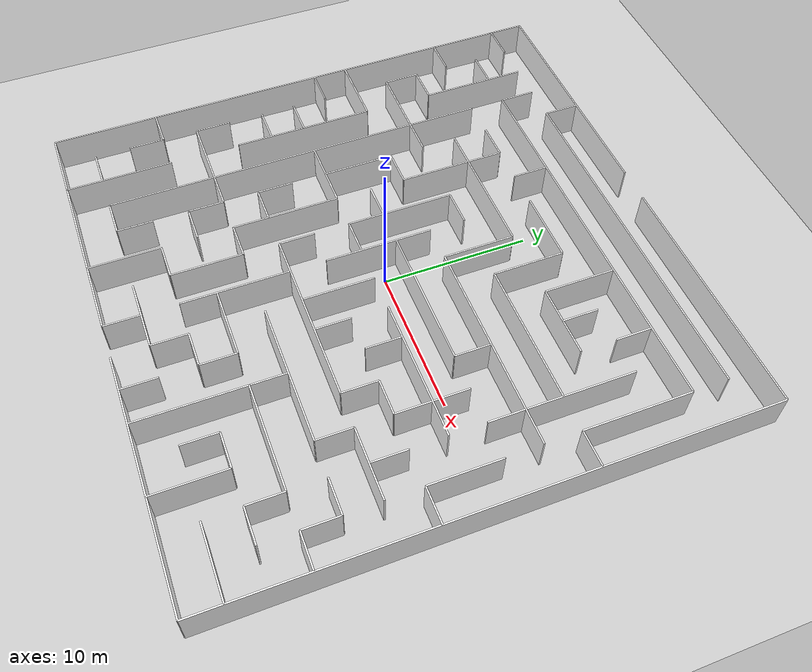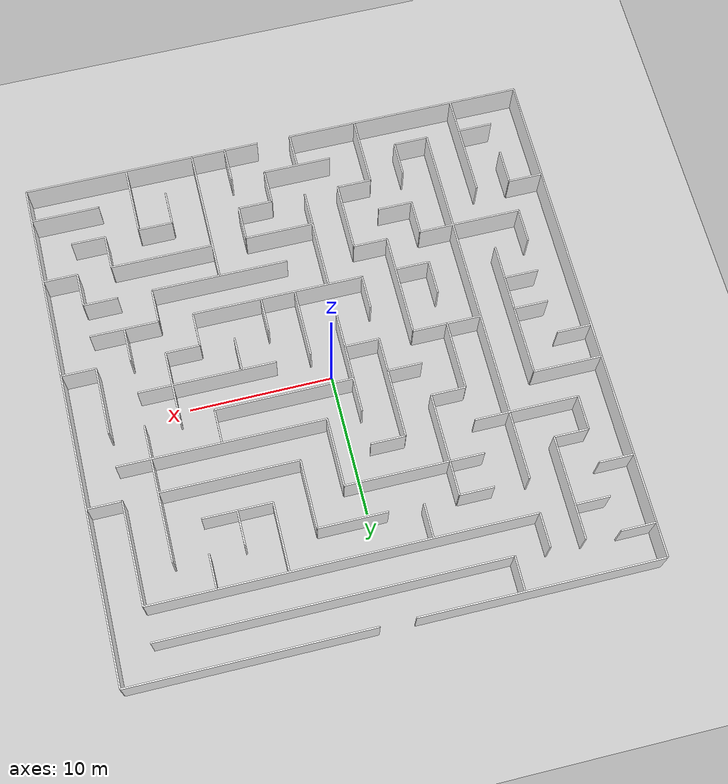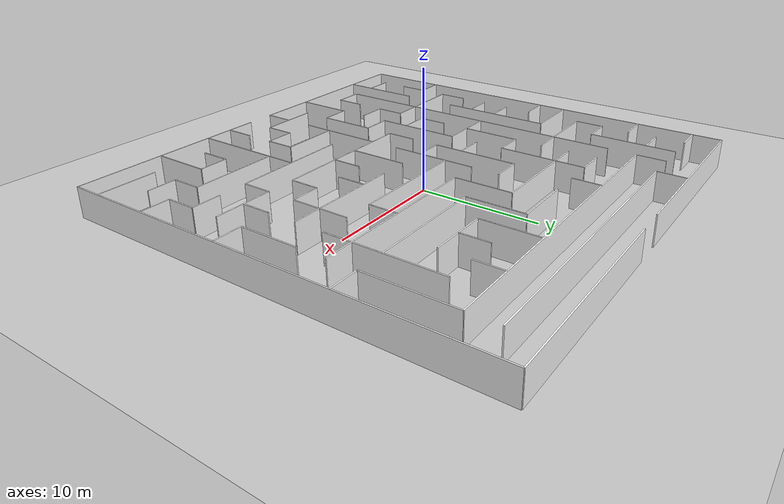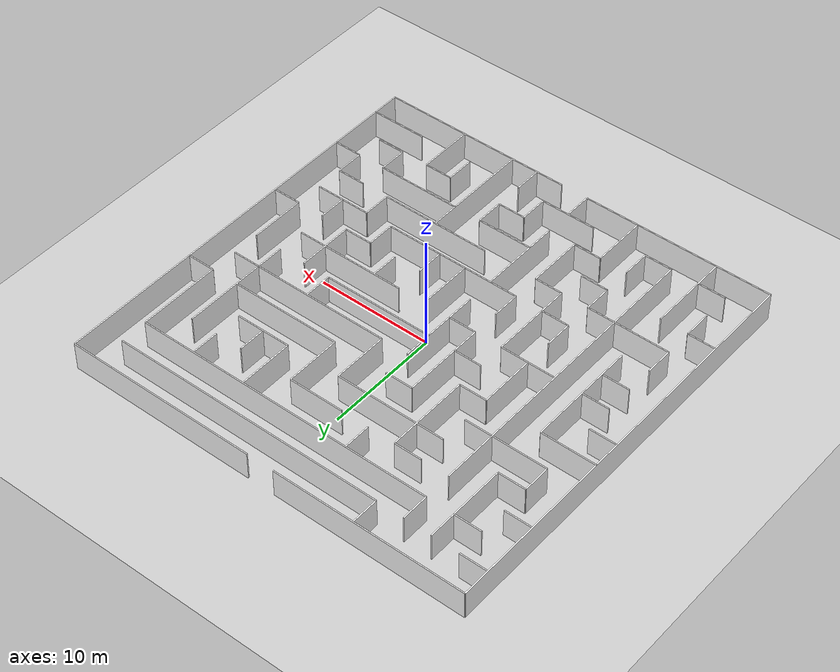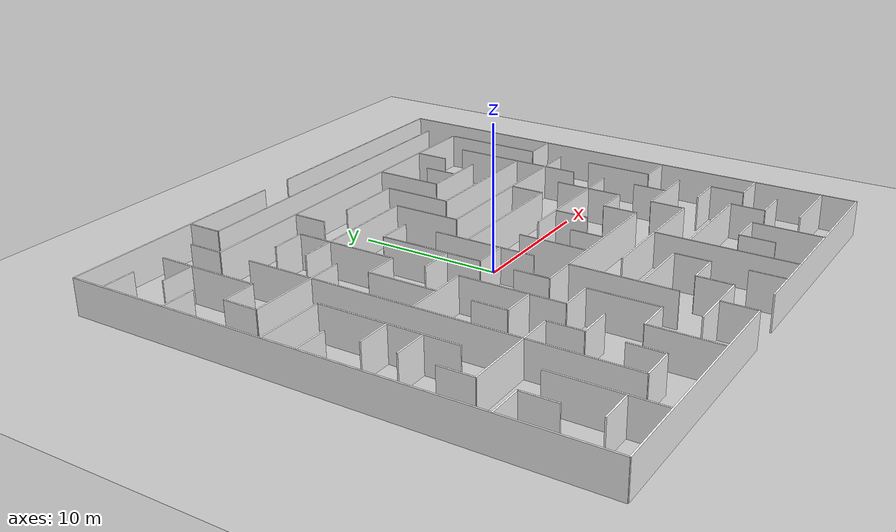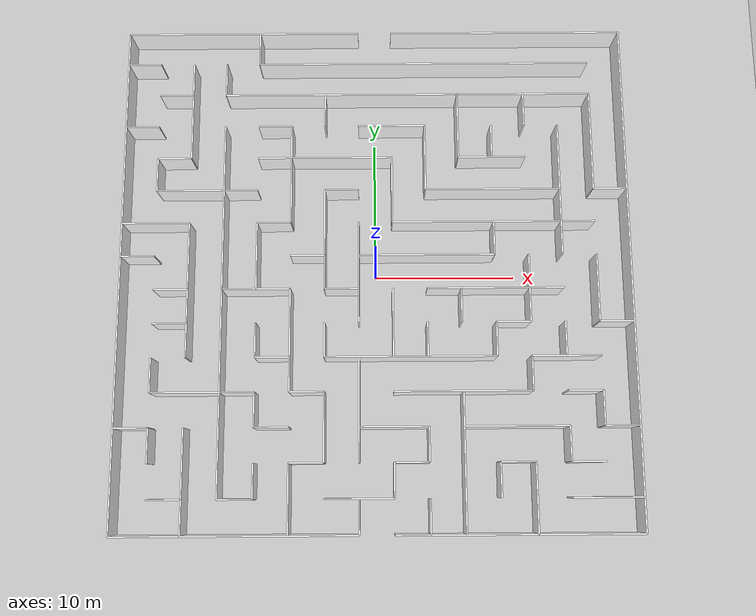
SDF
<sdf version='1.7'>
  <world name='default'>
    <light name='sun' type='directional'>
      <cast_shadows>1</cast_shadows>
      <pose>0 0 10 0 -0 0</pose>
      <diffuse>0.8 0.8 0.8 1</diffuse>
      <specular>0.2 0.2 0.2 1</specular>
      <attenuation>
        <range>1000</range>
        <constant>0.9</constant>
        <linear>0.01</linear>
        <quadratic>0.001</quadratic>
      </attenuation>
      <direction>-0.5 0.1 -0.9</direction>
      <spot>
        <inner_angle>0</inner_angle>
        <outer_angle>0</outer_angle>
        <falloff>0</falloff>
      </spot>
    </light>
    <model name='ground_plane'>
      <static>1</static>
      <link name='link'>
        <collision name='collision'>
          <geometry>
            <plane>
              <normal>0 0 1</normal>
              <size>100 100</size>
            </plane>
          </geometry>
          <surface>
            <contact>
              <collide_bitmask>65535</collide_bitmask>
              <ode/>
            </contact>
            <friction>
              <ode>
                <mu>100</mu>
                <mu2>50</mu2>
              </ode>
              <torsional><ode/></torsional>
            </friction>
            <bounce/>
          </surface>
          <max_contacts>10</max_contacts>
        </collision>
        <visual name='visual'>
          <cast_shadows>0</cast_shadows>
          <geometry>
            <plane>
              <normal>0 0 1</normal>
              <size>100 100</size>
            </plane>
          </geometry>
          <material>
            <script>
              <uri>file://media/materials/scripts/gazebo.material</uri>
              <n>Gazebo/Grey</n>
            </script>
          </material>
        </visual>
        <self_collide>0</self_collide>
        <enable_wind>0</enable_wind>
        <kinematic>0</kinematic>
      </link>
    </model>
    <gravity>0 0 -9.8</gravity>
    <magnetic_field>6e-06 2.3e-05 -4.2e-05</magnetic_field>
    <atmosphere type='adiabatic'/>
    <physics type='ode'>
      <max_step_size>0.001</max_step_size>
      <real_time_factor>1</real_time_factor>
      <real_time_update_rate>1000</real_time_update_rate>
    </physics>
    <scene>
      <ambient>0.4 0.4 0.4 1</ambient>
      <background>0.7 0.7 0.7 1</background>
      <shadows>1</shadows>
    </scene>
    <wind/>
    <spherical_coordinates>
      <surface_model>EARTH_WGS84</surface_model>
      <latitude_deg>0</latitude_deg>
      <longitude_deg>0</longitude_deg>
      <elevation>0</elevation>
      <heading_deg>0</heading_deg>
    </spherical_coordinates>
    <gui fullscreen='0'>
      <camera name='user_camera'>
        <pose>0 0 55 0 1.57 1.57</pose>
        <view_controller>orbit</view_controller>
        <projection_type>perspective</projection_type>
      </camera>
    </gui>
    <model name='maze_3'>
      <model name='maze_3'>
        <pose>0 0 0 0 -0 0</pose>
        <static>1</static>
        <link name='Wall_0'>
          <collision name='Wall_0_Collision'>
            <geometry>
              <box>
                <size>16.8000 0.1000 2.5000</size>
              </box>
            </geometry>
            <pose>0 0 1.2500 0 -0 0</pose>
            <max_contacts>10</max_contacts>
            <surface>
              <contact><ode/></contact>
              <bounce/>
              <friction><torsional><ode/></torsional><ode/></friction>
            </surface>
          </collision>
          <visual name='Wall_0_Visual'>
            <pose>0 0 1.2500 0 -0 0</pose>
            <geometry>
              <box>
                <size>16.8000 0.1000 2.5000</size>
              </box>
            </geometry>
            <material>
              <script>
                <uri>file://media/materials/scripts/gazebo.material</uri>
                <n>Gazebo/Grey</n>
              </script>
              <ambient>1 1 1 1</ambient>
            </material>
            <meta><layer>0</layer></meta>
          </visual>
          <pose>-9.600000 18.000000 0 0 -0 -0.00000</pose>
          <self_collide>0</self_collide>
          <enable_wind>0</enable_wind>
          <kinematic>0</kinematic>
        </link>
        <link name='Wall_1'>
          <collision name='Wall_1_Collision'>
            <geometry>
              <box>
                <size>16.8000 0.1000 2.5000</size>
              </box>
            </geometry>
            <pose>0 0 1.2500 0 -0 0</pose>
            <max_contacts>10</max_contacts>
            <surface>
              <contact><ode/></contact>
              <bounce/>
              <friction><torsional><ode/></torsional><ode/></friction>
            </surface>
          </collision>
          <visual name='Wall_1_Visual'>
            <pose>0 0 1.2500 0 -0 0</pose>
            <geometry>
              <box>
                <size>16.8000 0.1000 2.5000</size>
              </box>
            </geometry>
            <material>
              <script>
                <uri>file://media/materials/scripts/gazebo.material</uri>
                <n>Gazebo/Grey</n>
              </script>
              <ambient>1 1 1 1</ambient>
            </material>
            <meta><layer>0</layer></meta>
          </visual>
          <pose>9.600000 18.000000 0 0 -0 -0.00000</pose>
          <self_collide>0</self_collide>
          <enable_wind>0</enable_wind>
          <kinematic>0</kinematic>
        </link>
        <link name='Wall_2'>
          <collision name='Wall_2_Collision'>
            <geometry>
              <box>
                <size>2.4000 0.1000 2.5000</size>
              </box>
            </geometry>
            <pose>0 0 1.2500 0 -0 0</pose>
            <max_contacts>10</max_contacts>
            <surface>
              <contact><ode/></contact>
              <bounce/>
              <friction><torsional><ode/></torsional><ode/></friction>
            </surface>
          </collision>
          <visual name='Wall_2_Visual'>
            <pose>0 0 1.2500 0 -0 0</pose>
            <geometry>
              <box>
                <size>2.4000 0.1000 2.5000</size>
              </box>
            </geometry>
            <material>
              <script>
                <uri>file://media/materials/scripts/gazebo.material</uri>
                <n>Gazebo/Grey</n>
              </script>
              <ambient>1 1 1 1</ambient>
            </material>
            <meta><layer>0</layer></meta>
          </visual>
          <pose>-16.800000 15.600000 0 0 -0 -0.00000</pose>
          <self_collide>0</self_collide>
          <enable_wind>0</enable_wind>
          <kinematic>0</kinematic>
        </link>
        <link name='Wall_3'>
          <collision name='Wall_3_Collision'>
            <geometry>
              <box>
                <size>24.0000 0.1000 2.5000</size>
              </box>
            </geometry>
            <pose>0 0 1.2500 0 -0 0</pose>
            <max_contacts>10</max_contacts>
            <surface>
              <contact><ode/></contact>
              <bounce/>
              <friction><torsional><ode/></torsional><ode/></friction>
            </surface>
          </collision>
          <visual name='Wall_3_Visual'>
            <pose>0 0 1.2500 0 -0 0</pose>
            <geometry>
              <box>
                <size>24.0000 0.1000 2.5000</size>
              </box>
            </geometry>
            <material>
              <script>
                <uri>file://media/materials/scripts/gazebo.material</uri>
                <n>Gazebo/Grey</n>
              </script>
              <ambient>1 1 1 1</ambient>
            </material>
            <meta><layer>0</layer></meta>
          </visual>
          <pose>3.600000 15.600000 0 0 -0 -0.00000</pose>
          <self_collide>0</self_collide>
          <enable_wind>0</enable_wind>
          <kinematic>0</kinematic>
        </link>
        <link name='Wall_4'>
          <collision name='Wall_4_Collision'>
            <geometry>
              <box>
                <size>2.4000 0.1000 2.5000</size>
              </box>
            </geometry>
            <pose>0 0 1.2500 0 -0 0</pose>
            <max_contacts>10</max_contacts>
            <surface>
              <contact><ode/></contact>
              <bounce/>
              <friction><torsional><ode/></torsional><ode/></friction>
            </surface>
          </collision>
          <visual name='Wall_4_Visual'>
            <pose>0 0 1.2500 0 -0 0</pose>
            <geometry>
              <box>
                <size>2.4000 0.1000 2.5000</size>
              </box>
            </geometry>
            <material>
              <script>
                <uri>file://media/materials/scripts/gazebo.material</uri>
                <n>Gazebo/Grey</n>
              </script>
              <ambient>1 1 1 1</ambient>
            </material>
            <meta><layer>0</layer></meta>
          </visual>
          <pose>-14.400000 13.200000 0 0 -0 -0.00000</pose>
          <self_collide>0</self_collide>
          <enable_wind>0</enable_wind>
          <kinematic>0</kinematic>
        </link>
        <link name='Wall_5'>
          <collision name='Wall_5_Collision'>
            <geometry>
              <box>
                <size>26.4000 0.1000 2.5000</size>
              </box>
            </geometry>
            <pose>0 0 1.2500 0 -0 0</pose>
            <max_contacts>10</max_contacts>
            <surface>
              <contact><ode/></contact>
              <bounce/>
              <friction><torsional><ode/></torsional><ode/></friction>
            </surface>
          </collision>
          <visual name='Wall_5_Visual'>
            <pose>0 0 1.2500 0 -0 0</pose>
            <geometry>
              <box>
                <size>26.4000 0.1000 2.5000</size>
              </box>
            </geometry>
            <material>
              <script>
                <uri>file://media/materials/scripts/gazebo.material</uri>
                <n>Gazebo/Grey</n>
              </script>
              <ambient>1 1 1 1</ambient>
            </material>
            <meta><layer>0</layer></meta>
          </visual>
          <pose>2.400000 13.200000 0 0 -0 -0.00000</pose>
          <self_collide>0</self_collide>
          <enable_wind>0</enable_wind>
          <kinematic>0</kinematic>
        </link>
        <link name='Wall_6'>
          <collision name='Wall_6_Collision'>
            <geometry>
              <box>
                <size>2.4000 0.1000 2.5000</size>
              </box>
            </geometry>
            <pose>0 0 1.2500 0 -0 0</pose>
            <max_contacts>10</max_contacts>
            <surface>
              <contact><ode/></contact>
              <bounce/>
              <friction><torsional><ode/></torsional><ode/></friction>
            </surface>
          </collision>
          <visual name='Wall_6_Visual'>
            <pose>0 0 1.2500 0 -0 0</pose>
            <geometry>
              <box>
                <size>2.4000 0.1000 2.5000</size>
              </box>
            </geometry>
            <material>
              <script>
                <uri>file://media/materials/scripts/gazebo.material</uri>
                <n>Gazebo/Grey</n>
              </script>
              <ambient>1 1 1 1</ambient>
            </material>
            <meta><layer>0</layer></meta>
          </visual>
          <pose>-16.800000 10.800000 0 0 -0 -0.00000</pose>
          <self_collide>0</self_collide>
          <enable_wind>0</enable_wind>
          <kinematic>0</kinematic>
        </link>
        <link name='Wall_7'>
          <collision name='Wall_7_Collision'>
            <geometry>
              <box>
                <size>2.4000 0.1000 2.5000</size>
              </box>
            </geometry>
            <pose>0 0 1.2500 0 -0 0</pose>
            <max_contacts>10</max_contacts>
            <surface>
              <contact><ode/></contact>
              <bounce/>
              <friction><torsional><ode/></torsional><ode/></friction>
            </surface>
          </collision>
          <visual name='Wall_7_Visual'>
            <pose>0 0 1.2500 0 -0 0</pose>
            <geometry>
              <box>
                <size>2.4000 0.1000 2.5000</size>
              </box>
            </geometry>
            <material>
              <script>
                <uri>file://media/materials/scripts/gazebo.material</uri>
                <n>Gazebo/Grey</n>
              </script>
              <ambient>1 1 1 1</ambient>
            </material>
            <meta><layer>0</layer></meta>
          </visual>
          <pose>-7.200000 10.800000 0 0 -0 -0.00000</pose>
          <self_collide>0</self_collide>
          <enable_wind>0</enable_wind>
          <kinematic>0</kinematic>
        </link>
        <link name='Wall_8'>
          <collision name='Wall_8_Collision'>
            <geometry>
              <box>
                <size>4.8000 0.1000 2.5000</size>
              </box>
            </geometry>
            <pose>0 0 1.2500 0 -0 0</pose>
            <max_contacts>10</max_contacts>
            <surface>
              <contact><ode/></contact>
              <bounce/>
              <friction><torsional><ode/></torsional><ode/></friction>
            </surface>
          </collision>
          <visual name='Wall_8_Visual'>
            <pose>0 0 1.2500 0 -0 0</pose>
            <geometry>
              <box>
                <size>4.8000 0.1000 2.5000</size>
              </box>
            </geometry>
            <material>
              <script>
                <uri>file://media/materials/scripts/gazebo.material</uri>
                <n>Gazebo/Grey</n>
              </script>
              <ambient>1 1 1 1</ambient>
            </material>
            <meta><layer>0</layer></meta>
          </visual>
          <pose>1.200000 10.800000 0 0 -0 -0.00000</pose>
          <self_collide>0</self_collide>
          <enable_wind>0</enable_wind>
          <kinematic>0</kinematic>
        </link>
        <link name='Wall_9'>
          <collision name='Wall_9_Collision'>
            <geometry>
              <box>
                <size>2.4000 0.1000 2.5000</size>
              </box>
            </geometry>
            <pose>0 0 1.2500 0 -0 0</pose>
            <max_contacts>10</max_contacts>
            <surface>
              <contact><ode/></contact>
              <bounce/>
              <friction><torsional><ode/></torsional><ode/></friction>
            </surface>
          </collision>
          <visual name='Wall_9_Visual'>
            <pose>0 0 1.2500 0 -0 0</pose>
            <geometry>
              <box>
                <size>2.4000 0.1000 2.5000</size>
              </box>
            </geometry>
            <material>
              <script>
                <uri>file://media/materials/scripts/gazebo.material</uri>
                <n>Gazebo/Grey</n>
              </script>
              <ambient>1 1 1 1</ambient>
            </material>
            <meta><layer>0</layer></meta>
          </visual>
          <pose>-14.400000 8.400000 0 0 -0 -0.00000</pose>
          <self_collide>0</self_collide>
          <enable_wind>0</enable_wind>
          <kinematic>0</kinematic>
        </link>
        <link name='Wall_10'>
          <collision name='Wall_10_Collision'>
            <geometry>
              <box>
                <size>9.6000 0.1000 2.5000</size>
              </box>
            </geometry>
            <pose>0 0 1.2500 0 -0 0</pose>
            <max_contacts>10</max_contacts>
            <surface>
              <contact><ode/></contact>
              <bounce/>
              <friction><torsional><ode/></torsional><ode/></friction>
            </surface>
          </collision>
          <visual name='Wall_10_Visual'>
            <pose>0 0 1.2500 0 -0 0</pose>
            <geometry>
              <box>
                <size>9.6000 0.1000 2.5000</size>
              </box>
            </geometry>
            <material>
              <script>
                <uri>file://media/materials/scripts/gazebo.material</uri>
                <n>Gazebo/Grey</n>
              </script>
              <ambient>1 1 1 1</ambient>
            </material>
            <meta><layer>0</layer></meta>
          </visual>
          <pose>-3.600000 8.400000 0 0 -0 -0.00000</pose>
          <self_collide>0</self_collide>
          <enable_wind>0</enable_wind>
          <kinematic>0</kinematic>
        </link>
        <link name='Wall_11'>
          <collision name='Wall_11_Collision'>
            <geometry>
              <box>
                <size>4.8000 0.1000 2.5000</size>
              </box>
            </geometry>
            <pose>0 0 1.2500 0 -0 0</pose>
            <max_contacts>10</max_contacts>
            <surface>
              <contact><ode/></contact>
              <bounce/>
              <friction><torsional><ode/></torsional><ode/></friction>
            </surface>
          </collision>
          <visual name='Wall_11_Visual'>
            <pose>0 0 1.2500 0 -0 0</pose>
            <geometry>
              <box>
                <size>4.8000 0.1000 2.5000</size>
              </box>
            </geometry>
            <material>
              <script>
                <uri>file://media/materials/scripts/gazebo.material</uri>
                <n>Gazebo/Grey</n>
              </script>
              <ambient>1 1 1 1</ambient>
            </material>
            <meta><layer>0</layer></meta>
          </visual>
          <pose>8.400000 8.400000 0 0 -0 -0.00000</pose>
          <self_collide>0</self_collide>
          <enable_wind>0</enable_wind>
          <kinematic>0</kinematic>
        </link>
        <link name='Wall_12'>
          <collision name='Wall_12_Collision'>
            <geometry>
              <box>
                <size>7.2000 0.1000 2.5000</size>
              </box>
            </geometry>
            <pose>0 0 1.2500 0 -0 0</pose>
            <max_contacts>10</max_contacts>
            <surface>
              <contact><ode/></contact>
              <bounce/>
              <friction><torsional><ode/></torsional><ode/></friction>
            </surface>
          </collision>
          <visual name='Wall_12_Visual'>
            <pose>0 0 1.2500 0 -0 0</pose>
            <geometry>
              <box>
                <size>7.2000 0.1000 2.5000</size>
              </box>
            </geometry>
            <material>
              <script>
                <uri>file://media/materials/scripts/gazebo.material</uri>
                <n>Gazebo/Grey</n>
              </script>
              <ambient>1 1 1 1</ambient>
            </material>
            <meta><layer>0</layer></meta>
          </visual>
          <pose>-12.000000 6.000000 0 0 -0 -0.00000</pose>
          <self_collide>0</self_collide>
          <enable_wind>0</enable_wind>
          <kinematic>0</kinematic>
        </link>
        <link name='Wall_13'>
          <collision name='Wall_13_Collision'>
            <geometry>
              <box>
                <size>2.4000 0.1000 2.5000</size>
              </box>
            </geometry>
            <pose>0 0 1.2500 0 -0 0</pose>
            <max_contacts>10</max_contacts>
            <surface>
              <contact><ode/></contact>
              <bounce/>
              <friction><torsional><ode/></torsional><ode/></friction>
            </surface>
          </collision>
          <visual name='Wall_13_Visual'>
            <pose>0 0 1.2500 0 -0 0</pose>
            <geometry>
              <box>
                <size>2.4000 0.1000 2.5000</size>
              </box>
            </geometry>
            <material>
              <script>
                <uri>file://media/materials/scripts/gazebo.material</uri>
                <n>Gazebo/Grey</n>
              </script>
              <ambient>1 1 1 1</ambient>
            </material>
            <meta><layer>0</layer></meta>
          </visual>
          <pose>-2.400000 6.000000 0 0 -0 -0.00000</pose>
          <self_collide>0</self_collide>
          <enable_wind>0</enable_wind>
          <kinematic>0</kinematic>
        </link>
        <link name='Wall_14'>
          <collision name='Wall_14_Collision'>
            <geometry>
              <box>
                <size>9.6000 0.1000 2.5000</size>
              </box>
            </geometry>
            <pose>0 0 1.2500 0 -0 0</pose>
            <max_contacts>10</max_contacts>
            <surface>
              <contact><ode/></contact>
              <bounce/>
              <friction><torsional><ode/></torsional><ode/></friction>
            </surface>
          </collision>
          <visual name='Wall_14_Visual'>
            <pose>0 0 1.2500 0 -0 0</pose>
            <geometry>
              <box>
                <size>9.6000 0.1000 2.5000</size>
              </box>
            </geometry>
            <material>
              <script>
                <uri>file://media/materials/scripts/gazebo.material</uri>
                <n>Gazebo/Grey</n>
              </script>
              <ambient>1 1 1 1</ambient>
            </material>
            <meta><layer>0</layer></meta>
          </visual>
          <pose>8.400000 6.000000 0 0 -0 -0.00000</pose>
          <self_collide>0</self_collide>
          <enable_wind>0</enable_wind>
          <kinematic>0</kinematic>
        </link>
        <link name='Wall_15'>
          <collision name='Wall_15_Collision'>
            <geometry>
              <box>
                <size>2.4000 0.1000 2.5000</size>
              </box>
            </geometry>
            <pose>0 0 1.2500 0 -0 0</pose>
            <max_contacts>10</max_contacts>
            <surface>
              <contact><ode/></contact>
              <bounce/>
              <friction><torsional><ode/></torsional><ode/></friction>
            </surface>
          </collision>
          <visual name='Wall_15_Visual'>
            <pose>0 0 1.2500 0 -0 0</pose>
            <geometry>
              <box>
                <size>2.4000 0.1000 2.5000</size>
              </box>
            </geometry>
            <material>
              <script>
                <uri>file://media/materials/scripts/gazebo.material</uri>
                <n>Gazebo/Grey</n>
              </script>
              <ambient>1 1 1 1</ambient>
            </material>
            <meta><layer>0</layer></meta>
          </visual>
          <pose>16.800000 6.000000 0 0 -0 -0.00000</pose>
          <self_collide>0</self_collide>
          <enable_wind>0</enable_wind>
          <kinematic>0</kinematic>
        </link>
        <link name='Wall_16'>
          <collision name='Wall_16_Collision'>
            <geometry>
              <box>
                <size>4.8000 0.1000 2.5000</size>
              </box>
            </geometry>
            <pose>0 0 1.2500 0 -0 0</pose>
            <max_contacts>10</max_contacts>
            <surface>
              <contact><ode/></contact>
              <bounce/>
              <friction><torsional><ode/></torsional><ode/></friction>
            </surface>
          </collision>
          <visual name='Wall_16_Visual'>
            <pose>0 0 1.2500 0 -0 0</pose>
            <geometry>
              <box>
                <size>4.8000 0.1000 2.5000</size>
              </box>
            </geometry>
            <material>
              <script>
                <uri>file://media/materials/scripts/gazebo.material</uri>
                <n>Gazebo/Grey</n>
              </script>
              <ambient>1 1 1 1</ambient>
            </material>
            <meta><layer>0</layer></meta>
          </visual>
          <pose>-15.600000 3.600000 0 0 -0 -0.00000</pose>
          <self_collide>0</self_collide>
          <enable_wind>0</enable_wind>
          <kinematic>0</kinematic>
        </link>
        <link name='Wall_17'>
          <collision name='Wall_17_Collision'>
            <geometry>
              <box>
                <size>2.4000 0.1000 2.5000</size>
              </box>
            </geometry>
            <pose>0 0 1.2500 0 -0 0</pose>
            <max_contacts>10</max_contacts>
            <surface>
              <contact><ode/></contact>
              <bounce/>
              <friction><torsional><ode/></torsional><ode/></friction>
            </surface>
          </collision>
          <visual name='Wall_17_Visual'>
            <pose>0 0 1.2500 0 -0 0</pose>
            <geometry>
              <box>
                <size>2.4000 0.1000 2.5000</size>
              </box>
            </geometry>
            <material>
              <script>
                <uri>file://media/materials/scripts/gazebo.material</uri>
                <n>Gazebo/Grey</n>
              </script>
              <ambient>1 1 1 1</ambient>
            </material>
            <meta><layer>0</layer></meta>
          </visual>
          <pose>-7.200000 3.600000 0 0 -0 -0.00000</pose>
          <self_collide>0</self_collide>
          <enable_wind>0</enable_wind>
          <kinematic>0</kinematic>
        </link>
        <link name='Wall_18'>
          <collision name='Wall_18_Collision'>
            <geometry>
              <box>
                <size>14.4000 0.1000 2.5000</size>
              </box>
            </geometry>
            <pose>0 0 1.2500 0 -0 0</pose>
            <max_contacts>10</max_contacts>
            <surface>
              <contact><ode/></contact>
              <bounce/>
              <friction><torsional><ode/></torsional><ode/></friction>
            </surface>
          </collision>
          <visual name='Wall_18_Visual'>
            <pose>0 0 1.2500 0 -0 0</pose>
            <geometry>
              <box>
                <size>14.4000 0.1000 2.5000</size>
              </box>
            </geometry>
            <material>
              <script>
                <uri>file://media/materials/scripts/gazebo.material</uri>
                <n>Gazebo/Grey</n>
              </script>
              <ambient>1 1 1 1</ambient>
            </material>
            <meta><layer>0</layer></meta>
          </visual>
          <pose>8.400000 3.600000 0 0 -0 -0.00000</pose>
          <self_collide>0</self_collide>
          <enable_wind>0</enable_wind>
          <kinematic>0</kinematic>
        </link>
        <link name='Wall_19'>
          <collision name='Wall_19_Collision'>
            <geometry>
              <box>
                <size>2.4000 0.1000 2.5000</size>
              </box>
            </geometry>
            <pose>0 0 1.2500 0 -0 0</pose>
            <max_contacts>10</max_contacts>
            <surface>
              <contact><ode/></contact>
              <bounce/>
              <friction><torsional><ode/></torsional><ode/></friction>
            </surface>
          </collision>
          <visual name='Wall_19_Visual'>
            <pose>0 0 1.2500 0 -0 0</pose>
            <geometry>
              <box>
                <size>2.4000 0.1000 2.5000</size>
              </box>
            </geometry>
            <material>
              <script>
                <uri>file://media/materials/scripts/gazebo.material</uri>
                <n>Gazebo/Grey</n>
              </script>
              <ambient>1 1 1 1</ambient>
            </material>
            <meta><layer>0</layer></meta>
          </visual>
          <pose>-16.800000 1.200000 0 0 -0 -0.00000</pose>
          <self_collide>0</self_collide>
          <enable_wind>0</enable_wind>
          <kinematic>0</kinematic>
        </link>
        <link name='Wall_20'>
          <collision name='Wall_20_Collision'>
            <geometry>
              <box>
                <size>2.4000 0.1000 2.5000</size>
              </box>
            </geometry>
            <pose>0 0 1.2500 0 -0 0</pose>
            <max_contacts>10</max_contacts>
            <surface>
              <contact><ode/></contact>
              <bounce/>
              <friction><torsional><ode/></torsional><ode/></friction>
            </surface>
          </collision>
          <visual name='Wall_20_Visual'>
            <pose>0 0 1.2500 0 -0 0</pose>
            <geometry>
              <box>
                <size>2.4000 0.1000 2.5000</size>
              </box>
            </geometry>
            <material>
              <script>
                <uri>file://media/materials/scripts/gazebo.material</uri>
                <n>Gazebo/Grey</n>
              </script>
              <ambient>1 1 1 1</ambient>
            </material>
            <meta><layer>0</layer></meta>
          </visual>
          <pose>-4.800000 1.200000 0 0 -0 -0.00000</pose>
          <self_collide>0</self_collide>
          <enable_wind>0</enable_wind>
          <kinematic>0</kinematic>
        </link>
        <link name='Wall_21'>
          <collision name='Wall_21_Collision'>
            <geometry>
              <box>
                <size>9.6000 0.1000 2.5000</size>
              </box>
            </geometry>
            <pose>0 0 1.2500 0 -0 0</pose>
            <max_contacts>10</max_contacts>
            <surface>
              <contact><ode/></contact>
              <bounce/>
              <friction><torsional><ode/></torsional><ode/></friction>
            </surface>
          </collision>
          <visual name='Wall_21_Visual'>
            <pose>0 0 1.2500 0 -0 0</pose>
            <geometry>
              <box>
                <size>9.6000 0.1000 2.5000</size>
              </box>
            </geometry>
            <material>
              <script>
                <uri>file://media/materials/scripts/gazebo.material</uri>
                <n>Gazebo/Grey</n>
              </script>
              <ambient>1 1 1 1</ambient>
            </material>
            <meta><layer>0</layer></meta>
          </visual>
          <pose>3.600000 1.200000 0 0 -0 -0.00000</pose>
          <self_collide>0</self_collide>
          <enable_wind>0</enable_wind>
          <kinematic>0</kinematic>
        </link>
        <link name='Wall_22'>
          <collision name='Wall_22_Collision'>
            <geometry>
              <box>
                <size>2.4000 0.1000 2.5000</size>
              </box>
            </geometry>
            <pose>0 0 1.2500 0 -0 0</pose>
            <max_contacts>10</max_contacts>
            <surface>
              <contact><ode/></contact>
              <bounce/>
              <friction><torsional><ode/></torsional><ode/></friction>
            </surface>
          </collision>
          <visual name='Wall_22_Visual'>
            <pose>0 0 1.2500 0 -0 0</pose>
            <geometry>
              <box>
                <size>2.4000 0.1000 2.5000</size>
              </box>
            </geometry>
            <material>
              <script>
                <uri>file://media/materials/scripts/gazebo.material</uri>
                <n>Gazebo/Grey</n>
              </script>
              <ambient>1 1 1 1</ambient>
            </material>
            <meta><layer>0</layer></meta>
          </visual>
          <pose>-14.400000 -1.200000 0 0 -0 -0.00000</pose>
          <self_collide>0</self_collide>
          <enable_wind>0</enable_wind>
          <kinematic>0</kinematic>
        </link>
        <link name='Wall_23'>
          <collision name='Wall_23_Collision'>
            <geometry>
              <box>
                <size>4.8000 0.1000 2.5000</size>
              </box>
            </geometry>
            <pose>0 0 1.2500 0 -0 0</pose>
            <max_contacts>10</max_contacts>
            <surface>
              <contact><ode/></contact>
              <bounce/>
              <friction><torsional><ode/></torsional><ode/></friction>
            </surface>
          </collision>
          <visual name='Wall_23_Visual'>
            <pose>0 0 1.2500 0 -0 0</pose>
            <geometry>
              <box>
                <size>4.8000 0.1000 2.5000</size>
              </box>
            </geometry>
            <material>
              <script>
                <uri>file://media/materials/scripts/gazebo.material</uri>
                <n>Gazebo/Grey</n>
              </script>
              <ambient>1 1 1 1</ambient>
            </material>
            <meta><layer>0</layer></meta>
          </visual>
          <pose>-8.400000 -1.200000 0 0 -0 -0.00000</pose>
          <self_collide>0</self_collide>
          <enable_wind>0</enable_wind>
          <kinematic>0</kinematic>
        </link>
        <link name='Wall_24'>
          <collision name='Wall_24_Collision'>
            <geometry>
              <box>
                <size>2.4000 0.1000 2.5000</size>
              </box>
            </geometry>
            <pose>0 0 1.2500 0 -0 0</pose>
            <max_contacts>10</max_contacts>
            <surface>
              <contact><ode/></contact>
              <bounce/>
              <friction><torsional><ode/></torsional><ode/></friction>
            </surface>
          </collision>
          <visual name='Wall_24_Visual'>
            <pose>0 0 1.2500 0 -0 0</pose>
            <geometry>
              <box>
                <size>2.4000 0.1000 2.5000</size>
              </box>
            </geometry>
            <material>
              <script>
                <uri>file://media/materials/scripts/gazebo.material</uri>
                <n>Gazebo/Grey</n>
              </script>
              <ambient>1 1 1 1</ambient>
            </material>
            <meta><layer>0</layer></meta>
          </visual>
          <pose>-2.400000 -1.200000 0 0 -0 -0.00000</pose>
          <self_collide>0</self_collide>
          <enable_wind>0</enable_wind>
          <kinematic>0</kinematic>
        </link>
        <link name='Wall_25'>
          <collision name='Wall_25_Collision'>
            <geometry>
              <box>
                <size>9.6000 0.1000 2.5000</size>
              </box>
            </geometry>
            <pose>0 0 1.2500 0 -0 0</pose>
            <max_contacts>10</max_contacts>
            <surface>
              <contact><ode/></contact>
              <bounce/>
              <friction><torsional><ode/></torsional><ode/></friction>
            </surface>
          </collision>
          <visual name='Wall_25_Visual'>
            <pose>0 0 1.2500 0 -0 0</pose>
            <geometry>
              <box>
                <size>9.6000 0.1000 2.5000</size>
              </box>
            </geometry>
            <material>
              <script>
                <uri>file://media/materials/scripts/gazebo.material</uri>
                <n>Gazebo/Grey</n>
              </script>
              <ambient>1 1 1 1</ambient>
            </material>
            <meta><layer>0</layer></meta>
          </visual>
          <pose>8.400000 -1.200000 0 0 -0 -0.00000</pose>
          <self_collide>0</self_collide>
          <enable_wind>0</enable_wind>
          <kinematic>0</kinematic>
        </link>
        <link name='Wall_26'>
          <collision name='Wall_26_Collision'>
            <geometry>
              <box>
                <size>2.4000 0.1000 2.5000</size>
              </box>
            </geometry>
            <pose>0 0 1.2500 0 -0 0</pose>
            <max_contacts>10</max_contacts>
            <surface>
              <contact><ode/></contact>
              <bounce/>
              <friction><torsional><ode/></torsional><ode/></friction>
            </surface>
          </collision>
          <visual name='Wall_26_Visual'>
            <pose>0 0 1.2500 0 -0 0</pose>
            <geometry>
              <box>
                <size>2.4000 0.1000 2.5000</size>
              </box>
            </geometry>
            <material>
              <script>
                <uri>file://media/materials/scripts/gazebo.material</uri>
                <n>Gazebo/Grey</n>
              </script>
              <ambient>1 1 1 1</ambient>
            </material>
            <meta><layer>0</layer></meta>
          </visual>
          <pose>-14.400000 -3.600000 0 0 -0 -0.00000</pose>
          <self_collide>0</self_collide>
          <enable_wind>0</enable_wind>
          <kinematic>0</kinematic>
        </link>
        <link name='Wall_27'>
          <collision name='Wall_27_Collision'>
            <geometry>
              <box>
                <size>2.4000 0.1000 2.5000</size>
              </box>
            </geometry>
            <pose>0 0 1.2500 0 -0 0</pose>
            <max_contacts>10</max_contacts>
            <surface>
              <contact><ode/></contact>
              <bounce/>
              <friction><torsional><ode/></torsional><ode/></friction>
            </surface>
          </collision>
          <visual name='Wall_27_Visual'>
            <pose>0 0 1.2500 0 -0 0</pose>
            <geometry>
              <box>
                <size>2.4000 0.1000 2.5000</size>
              </box>
            </geometry>
            <material>
              <script>
                <uri>file://media/materials/scripts/gazebo.material</uri>
                <n>Gazebo/Grey</n>
              </script>
              <ambient>1 1 1 1</ambient>
            </material>
            <meta><layer>0</layer></meta>
          </visual>
          <pose>9.600000 -3.600000 0 0 -0 -0.00000</pose>
          <self_collide>0</self_collide>
          <enable_wind>0</enable_wind>
          <kinematic>0</kinematic>
        </link>
        <link name='Wall_28'>
          <collision name='Wall_28_Collision'>
            <geometry>
              <box>
                <size>2.4000 0.1000 2.5000</size>
              </box>
            </geometry>
            <pose>0 0 1.2500 0 -0 0</pose>
            <max_contacts>10</max_contacts>
            <surface>
              <contact><ode/></contact>
              <bounce/>
              <friction><torsional><ode/></torsional><ode/></friction>
            </surface>
          </collision>
          <visual name='Wall_28_Visual'>
            <pose>0 0 1.2500 0 -0 0</pose>
            <geometry>
              <box>
                <size>2.4000 0.1000 2.5000</size>
              </box>
            </geometry>
            <material>
              <script>
                <uri>file://media/materials/scripts/gazebo.material</uri>
                <n>Gazebo/Grey</n>
              </script>
              <ambient>1 1 1 1</ambient>
            </material>
            <meta><layer>0</layer></meta>
          </visual>
          <pose>16.800000 -3.600000 0 0 -0 -0.00000</pose>
          <self_collide>0</self_collide>
          <enable_wind>0</enable_wind>
          <kinematic>0</kinematic>
        </link>
        <link name='Wall_29'>
          <collision name='Wall_29_Collision'>
            <geometry>
              <box>
                <size>2.4000 0.1000 2.5000</size>
              </box>
            </geometry>
            <pose>0 0 1.2500 0 -0 0</pose>
            <max_contacts>10</max_contacts>
            <surface>
              <contact><ode/></contact>
              <bounce/>
              <friction><torsional><ode/></torsional><ode/></friction>
            </surface>
          </collision>
          <visual name='Wall_29_Visual'>
            <pose>0 0 1.2500 0 -0 0</pose>
            <geometry>
              <box>
                <size>2.4000 0.1000 2.5000</size>
              </box>
            </geometry>
            <material>
              <script>
                <uri>file://media/materials/scripts/gazebo.material</uri>
                <n>Gazebo/Grey</n>
              </script>
              <ambient>1 1 1 1</ambient>
            </material>
            <meta><layer>0</layer></meta>
          </visual>
          <pose>-7.200000 -6.000000 0 0 -0 -0.00000</pose>
          <self_collide>0</self_collide>
          <enable_wind>0</enable_wind>
          <kinematic>0</kinematic>
        </link>
        <link name='Wall_30'>
          <collision name='Wall_30_Collision'>
            <geometry>
              <box>
                <size>12.0000 0.1000 2.5000</size>
              </box>
            </geometry>
            <pose>0 0 1.2500 0 -0 0</pose>
            <max_contacts>10</max_contacts>
            <surface>
              <contact><ode/></contact>
              <bounce/>
              <friction><torsional><ode/></torsional><ode/></friction>
            </surface>
          </collision>
          <visual name='Wall_30_Visual'>
            <pose>0 0 1.2500 0 -0 0</pose>
            <geometry>
              <box>
                <size>12.0000 0.1000 2.5000</size>
              </box>
            </geometry>
            <material>
              <script>
                <uri>file://media/materials/scripts/gazebo.material</uri>
                <n>Gazebo/Grey</n>
              </script>
              <ambient>1 1 1 1</ambient>
            </material>
            <meta><layer>0</layer></meta>
          </visual>
          <pose>2.400000 -6.000000 0 0 -0 -0.00000</pose>
          <self_collide>0</self_collide>
          <enable_wind>0</enable_wind>
          <kinematic>0</kinematic>
        </link>
        <link name='Wall_31'>
          <collision name='Wall_31_Collision'>
            <geometry>
              <box>
                <size>4.8000 0.1000 2.5000</size>
              </box>
            </geometry>
            <pose>0 0 1.2500 0 -0 0</pose>
            <max_contacts>10</max_contacts>
            <surface>
              <contact><ode/></contact>
              <bounce/>
              <friction><torsional><ode/></torsional><ode/></friction>
            </surface>
          </collision>
          <visual name='Wall_31_Visual'>
            <pose>0 0 1.2500 0 -0 0</pose>
            <geometry>
              <box>
                <size>4.8000 0.1000 2.5000</size>
              </box>
            </geometry>
            <material>
              <script>
                <uri>file://media/materials/scripts/gazebo.material</uri>
                <n>Gazebo/Grey</n>
              </script>
              <ambient>1 1 1 1</ambient>
            </material>
            <meta><layer>0</layer></meta>
          </visual>
          <pose>13.200000 -6.000000 0 0 -0 -0.00000</pose>
          <self_collide>0</self_collide>
          <enable_wind>0</enable_wind>
          <kinematic>0</kinematic>
        </link>
        <link name='Wall_32'>
          <collision name='Wall_32_Collision'>
            <geometry>
              <box>
                <size>7.2000 0.1000 2.5000</size>
              </box>
            </geometry>
            <pose>0 0 1.2500 0 -0 0</pose>
            <max_contacts>10</max_contacts>
            <surface>
              <contact><ode/></contact>
              <bounce/>
              <friction><torsional><ode/></torsional><ode/></friction>
            </surface>
          </collision>
          <visual name='Wall_32_Visual'>
            <pose>0 0 1.2500 0 -0 0</pose>
            <geometry>
              <box>
                <size>7.2000 0.1000 2.5000</size>
              </box>
            </geometry>
            <material>
              <script>
                <uri>file://media/materials/scripts/gazebo.material</uri>
                <n>Gazebo/Grey</n>
              </script>
              <ambient>1 1 1 1</ambient>
            </material>
            <meta><layer>0</layer></meta>
          </visual>
          <pose>-12.000000 -8.400000 0 0 -0 -0.00000</pose>
          <self_collide>0</self_collide>
          <enable_wind>0</enable_wind>
          <kinematic>0</kinematic>
        </link>
        <link name='Wall_33'>
          <collision name='Wall_33_Collision'>
            <geometry>
              <box>
                <size>2.4000 0.1000 2.5000</size>
              </box>
            </geometry>
            <pose>0 0 1.2500 0 -0 0</pose>
            <max_contacts>10</max_contacts>
            <surface>
              <contact><ode/></contact>
              <bounce/>
              <friction><torsional><ode/></torsional><ode/></friction>
            </surface>
          </collision>
          <visual name='Wall_33_Visual'>
            <pose>0 0 1.2500 0 -0 0</pose>
            <geometry>
              <box>
                <size>2.4000 0.1000 2.5000</size>
              </box>
            </geometry>
            <material>
              <script>
                <uri>file://media/materials/scripts/gazebo.material</uri>
                <n>Gazebo/Grey</n>
              </script>
              <ambient>1 1 1 1</ambient>
            </material>
            <meta><layer>0</layer></meta>
          </visual>
          <pose>-4.800000 -8.400000 0 0 -0 -0.00000</pose>
          <self_collide>0</self_collide>
          <enable_wind>0</enable_wind>
          <kinematic>0</kinematic>
        </link>
        <link name='Wall_34'>
          <collision name='Wall_34_Collision'>
            <geometry>
              <box>
                <size>9.6000 0.1000 2.5000</size>
              </box>
            </geometry>
            <pose>0 0 1.2500 0 -0 0</pose>
            <max_contacts>10</max_contacts>
            <surface>
              <contact><ode/></contact>
              <bounce/>
              <friction><torsional><ode/></torsional><ode/></friction>
            </surface>
          </collision>
          <visual name='Wall_34_Visual'>
            <pose>0 0 1.2500 0 -0 0</pose>
            <geometry>
              <box>
                <size>9.6000 0.1000 2.5000</size>
              </box>
            </geometry>
            <material>
              <script>
                <uri>file://media/materials/scripts/gazebo.material</uri>
                <n>Gazebo/Grey</n>
              </script>
              <ambient>1 1 1 1</ambient>
            </material>
            <meta><layer>0</layer></meta>
          </visual>
          <pose>6.000000 -8.400000 0 0 -0 -0.00000</pose>
          <self_collide>0</self_collide>
          <enable_wind>0</enable_wind>
          <kinematic>0</kinematic>
        </link>
        <link name='Wall_35'>
          <collision name='Wall_35_Collision'>
            <geometry>
              <box>
                <size>2.4000 0.1000 2.5000</size>
              </box>
            </geometry>
            <pose>0 0 1.2500 0 -0 0</pose>
            <max_contacts>10</max_contacts>
            <surface>
              <contact><ode/></contact>
              <bounce/>
              <friction><torsional><ode/></torsional><ode/></friction>
            </surface>
          </collision>
          <visual name='Wall_35_Visual'>
            <pose>0 0 1.2500 0 -0 0</pose>
            <geometry>
              <box>
                <size>2.4000 0.1000 2.5000</size>
              </box>
            </geometry>
            <material>
              <script>
                <uri>file://media/materials/scripts/gazebo.material</uri>
                <n>Gazebo/Grey</n>
              </script>
              <ambient>1 1 1 1</ambient>
            </material>
            <meta><layer>0</layer></meta>
          </visual>
          <pose>14.400000 -8.400000 0 0 -0 -0.00000</pose>
          <self_collide>0</self_collide>
          <enable_wind>0</enable_wind>
          <kinematic>0</kinematic>
        </link>
        <link name='Wall_36'>
          <collision name='Wall_36_Collision'>
            <geometry>
              <box>
                <size>2.4000 0.1000 2.5000</size>
              </box>
            </geometry>
            <pose>0 0 1.2500 0 -0 0</pose>
            <max_contacts>10</max_contacts>
            <surface>
              <contact><ode/></contact>
              <bounce/>
              <friction><torsional><ode/></torsional><ode/></friction>
            </surface>
          </collision>
          <visual name='Wall_36_Visual'>
            <pose>0 0 1.2500 0 -0 0</pose>
            <geometry>
              <box>
                <size>2.4000 0.1000 2.5000</size>
              </box>
            </geometry>
            <material>
              <script>
                <uri>file://media/materials/scripts/gazebo.material</uri>
                <n>Gazebo/Grey</n>
              </script>
              <ambient>1 1 1 1</ambient>
            </material>
            <meta><layer>0</layer></meta>
          </visual>
          <pose>-16.800000 -10.800000 0 0 -0 -0.00000</pose>
          <self_collide>0</self_collide>
          <enable_wind>0</enable_wind>
          <kinematic>0</kinematic>
        </link>
        <link name='Wall_37'>
          <collision name='Wall_37_Collision'>
            <geometry>
              <box>
                <size>2.4000 0.1000 2.5000</size>
              </box>
            </geometry>
            <pose>0 0 1.2500 0 -0 0</pose>
            <max_contacts>10</max_contacts>
            <surface>
              <contact><ode/></contact>
              <bounce/>
              <friction><torsional><ode/></torsional><ode/></friction>
            </surface>
          </collision>
          <visual name='Wall_37_Visual'>
            <pose>0 0 1.2500 0 -0 0</pose>
            <geometry>
              <box>
                <size>2.4000 0.1000 2.5000</size>
              </box>
            </geometry>
            <material>
              <script>
                <uri>file://media/materials/scripts/gazebo.material</uri>
                <n>Gazebo/Grey</n>
              </script>
              <ambient>1 1 1 1</ambient>
            </material>
            <meta><layer>0</layer></meta>
          </visual>
          <pose>-7.200000 -10.800000 0 0 -0 -0.00000</pose>
          <self_collide>0</self_collide>
          <enable_wind>0</enable_wind>
          <kinematic>0</kinematic>
        </link>
        <link name='Wall_38'>
          <collision name='Wall_38_Collision'>
            <geometry>
              <box>
                <size>4.8000 0.1000 2.5000</size>
              </box>
            </geometry>
            <pose>0 0 1.2500 0 -0 0</pose>
            <max_contacts>10</max_contacts>
            <surface>
              <contact><ode/></contact>
              <bounce/>
              <friction><torsional><ode/></torsional><ode/></friction>
            </surface>
          </collision>
          <visual name='Wall_38_Visual'>
            <pose>0 0 1.2500 0 -0 0</pose>
            <geometry>
              <box>
                <size>4.8000 0.1000 2.5000</size>
              </box>
            </geometry>
            <material>
              <script>
                <uri>file://media/materials/scripts/gazebo.material</uri>
                <n>Gazebo/Grey</n>
              </script>
              <ambient>1 1 1 1</ambient>
            </material>
            <meta><layer>0</layer></meta>
          </visual>
          <pose>1.200000 -10.800000 0 0 -0 -0.00000</pose>
          <self_collide>0</self_collide>
          <enable_wind>0</enable_wind>
          <kinematic>0</kinematic>
        </link>
        <link name='Wall_39'>
          <collision name='Wall_39_Collision'>
            <geometry>
              <box>
                <size>7.2000 0.1000 2.5000</size>
              </box>
            </geometry>
            <pose>0 0 1.2500 0 -0 0</pose>
            <max_contacts>10</max_contacts>
            <surface>
              <contact><ode/></contact>
              <bounce/>
              <friction><torsional><ode/></torsional><ode/></friction>
            </surface>
          </collision>
          <visual name='Wall_39_Visual'>
            <pose>0 0 1.2500 0 -0 0</pose>
            <geometry>
              <box>
                <size>7.2000 0.1000 2.5000</size>
              </box>
            </geometry>
            <material>
              <script>
                <uri>file://media/materials/scripts/gazebo.material</uri>
                <n>Gazebo/Grey</n>
              </script>
              <ambient>1 1 1 1</ambient>
            </material>
            <meta><layer>0</layer></meta>
          </visual>
          <pose>9.600000 -10.800000 0 0 -0 -0.00000</pose>
          <self_collide>0</self_collide>
          <enable_wind>0</enable_wind>
          <kinematic>0</kinematic>
        </link>
        <link name='Wall_40'>
          <collision name='Wall_40_Collision'>
            <geometry>
              <box>
                <size>2.4000 0.1000 2.5000</size>
              </box>
            </geometry>
            <pose>0 0 1.2500 0 -0 0</pose>
            <max_contacts>10</max_contacts>
            <surface>
              <contact><ode/></contact>
              <bounce/>
              <friction><torsional><ode/></torsional><ode/></friction>
            </surface>
          </collision>
          <visual name='Wall_40_Visual'>
            <pose>0 0 1.2500 0 -0 0</pose>
            <geometry>
              <box>
                <size>2.4000 0.1000 2.5000</size>
              </box>
            </geometry>
            <material>
              <script>
                <uri>file://media/materials/scripts/gazebo.material</uri>
                <n>Gazebo/Grey</n>
              </script>
              <ambient>1 1 1 1</ambient>
            </material>
            <meta><layer>0</layer></meta>
          </visual>
          <pose>16.800000 -10.800000 0 0 -0 -0.00000</pose>
          <self_collide>0</self_collide>
          <enable_wind>0</enable_wind>
          <kinematic>0</kinematic>
        </link>
        <link name='Wall_41'>
          <collision name='Wall_41_Collision'>
            <geometry>
              <box>
                <size>2.4000 0.1000 2.5000</size>
              </box>
            </geometry>
            <pose>0 0 1.2500 0 -0 0</pose>
            <max_contacts>10</max_contacts>
            <surface>
              <contact><ode/></contact>
              <bounce/>
              <friction><torsional><ode/></torsional><ode/></friction>
            </surface>
          </collision>
          <visual name='Wall_41_Visual'>
            <pose>0 0 1.2500 0 -0 0</pose>
            <geometry>
              <box>
                <size>2.4000 0.1000 2.5000</size>
              </box>
            </geometry>
            <material>
              <script>
                <uri>file://media/materials/scripts/gazebo.material</uri>
                <n>Gazebo/Grey</n>
              </script>
              <ambient>1 1 1 1</ambient>
            </material>
            <meta><layer>0</layer></meta>
          </visual>
          <pose>-4.800000 -13.200000 0 0 -0 -0.00000</pose>
          <self_collide>0</self_collide>
          <enable_wind>0</enable_wind>
          <kinematic>0</kinematic>
        </link>
        <link name='Wall_42'>
          <collision name='Wall_42_Collision'>
            <geometry>
              <box>
                <size>2.4000 0.1000 2.5000</size>
              </box>
            </geometry>
            <pose>0 0 1.2500 0 -0 0</pose>
            <max_contacts>10</max_contacts>
            <surface>
              <contact><ode/></contact>
              <bounce/>
              <friction><torsional><ode/></torsional><ode/></friction>
            </surface>
          </collision>
          <visual name='Wall_42_Visual'>
            <pose>0 0 1.2500 0 -0 0</pose>
            <geometry>
              <box>
                <size>2.4000 0.1000 2.5000</size>
              </box>
            </geometry>
            <material>
              <script>
                <uri>file://media/materials/scripts/gazebo.material</uri>
                <n>Gazebo/Grey</n>
              </script>
              <ambient>1 1 1 1</ambient>
            </material>
            <meta><layer>0</layer></meta>
          </visual>
          <pose>2.400000 -13.200000 0 0 -0 -0.00000</pose>
          <self_collide>0</self_collide>
          <enable_wind>0</enable_wind>
          <kinematic>0</kinematic>
        </link>
        <link name='Wall_43'>
          <collision name='Wall_43_Collision'>
            <geometry>
              <box>
                <size>2.4000 0.1000 2.5000</size>
              </box>
            </geometry>
            <pose>0 0 1.2500 0 -0 0</pose>
            <max_contacts>10</max_contacts>
            <surface>
              <contact><ode/></contact>
              <bounce/>
              <friction><torsional><ode/></torsional><ode/></friction>
            </surface>
          </collision>
          <visual name='Wall_43_Visual'>
            <pose>0 0 1.2500 0 -0 0</pose>
            <geometry>
              <box>
                <size>2.4000 0.1000 2.5000</size>
              </box>
            </geometry>
            <material>
              <script>
                <uri>file://media/materials/scripts/gazebo.material</uri>
                <n>Gazebo/Grey</n>
              </script>
              <ambient>1 1 1 1</ambient>
            </material>
            <meta><layer>0</layer></meta>
          </visual>
          <pose>9.600000 -13.200000 0 0 -0 -0.00000</pose>
          <self_collide>0</self_collide>
          <enable_wind>0</enable_wind>
          <kinematic>0</kinematic>
        </link>
        <link name='Wall_44'>
          <collision name='Wall_44_Collision'>
            <geometry>
              <box>
                <size>2.4000 0.1000 2.5000</size>
              </box>
            </geometry>
            <pose>0 0 1.2500 0 -0 0</pose>
            <max_contacts>10</max_contacts>
            <surface>
              <contact><ode/></contact>
              <bounce/>
              <friction><torsional><ode/></torsional><ode/></friction>
            </surface>
          </collision>
          <visual name='Wall_44_Visual'>
            <pose>0 0 1.2500 0 -0 0</pose>
            <geometry>
              <box>
                <size>2.4000 0.1000 2.5000</size>
              </box>
            </geometry>
            <material>
              <script>
                <uri>file://media/materials/scripts/gazebo.material</uri>
                <n>Gazebo/Grey</n>
              </script>
              <ambient>1 1 1 1</ambient>
            </material>
            <meta><layer>0</layer></meta>
          </visual>
          <pose>14.400000 -13.200000 0 0 -0 -0.00000</pose>
          <self_collide>0</self_collide>
          <enable_wind>0</enable_wind>
          <kinematic>0</kinematic>
        </link>
        <link name='Wall_45'>
          <collision name='Wall_45_Collision'>
            <geometry>
              <box>
                <size>2.4000 0.1000 2.5000</size>
              </box>
            </geometry>
            <pose>0 0 1.2500 0 -0 0</pose>
            <max_contacts>10</max_contacts>
            <surface>
              <contact><ode/></contact>
              <bounce/>
              <friction><torsional><ode/></torsional><ode/></friction>
            </surface>
          </collision>
          <visual name='Wall_45_Visual'>
            <pose>0 0 1.2500 0 -0 0</pose>
            <geometry>
              <box>
                <size>2.4000 0.1000 2.5000</size>
              </box>
            </geometry>
            <material>
              <script>
                <uri>file://media/materials/scripts/gazebo.material</uri>
                <n>Gazebo/Grey</n>
              </script>
              <ambient>1 1 1 1</ambient>
            </material>
            <meta><layer>0</layer></meta>
          </visual>
          <pose>-14.400000 -15.600000 0 0 -0 -0.00000</pose>
          <self_collide>0</self_collide>
          <enable_wind>0</enable_wind>
          <kinematic>0</kinematic>
        </link>
        <link name='Wall_46'>
          <collision name='Wall_46_Collision'>
            <geometry>
              <box>
                <size>2.4000 0.1000 2.5000</size>
              </box>
            </geometry>
            <pose>0 0 1.2500 0 -0 0</pose>
            <max_contacts>10</max_contacts>
            <surface>
              <contact><ode/></contact>
              <bounce/>
              <friction><torsional><ode/></torsional><ode/></friction>
            </surface>
          </collision>
          <visual name='Wall_46_Visual'>
            <pose>0 0 1.2500 0 -0 0</pose>
            <geometry>
              <box>
                <size>2.4000 0.1000 2.5000</size>
              </box>
            </geometry>
            <material>
              <script>
                <uri>file://media/materials/scripts/gazebo.material</uri>
                <n>Gazebo/Grey</n>
              </script>
              <ambient>1 1 1 1</ambient>
            </material>
            <meta><layer>0</layer></meta>
          </visual>
          <pose>-9.600000 -15.600000 0 0 -0 -0.00000</pose>
          <self_collide>0</self_collide>
          <enable_wind>0</enable_wind>
          <kinematic>0</kinematic>
        </link>
        <link name='Wall_47'>
          <collision name='Wall_47_Collision'>
            <geometry>
              <box>
                <size>4.8000 0.1000 2.5000</size>
              </box>
            </geometry>
            <pose>0 0 1.2500 0 -0 0</pose>
            <max_contacts>10</max_contacts>
            <surface>
              <contact><ode/></contact>
              <bounce/>
              <friction><torsional><ode/></torsional><ode/></friction>
            </surface>
          </collision>
          <visual name='Wall_47_Visual'>
            <pose>0 0 1.2500 0 -0 0</pose>
            <geometry>
              <box>
                <size>4.8000 0.1000 2.5000</size>
              </box>
            </geometry>
            <material>
              <script>
                <uri>file://media/materials/scripts/gazebo.material</uri>
                <n>Gazebo/Grey</n>
              </script>
              <ambient>1 1 1 1</ambient>
            </material>
            <meta><layer>0</layer></meta>
          </visual>
          <pose>-1.200000 -15.600000 0 0 -0 -0.00000</pose>
          <self_collide>0</self_collide>
          <enable_wind>0</enable_wind>
          <kinematic>0</kinematic>
        </link>
        <link name='Wall_48'>
          <collision name='Wall_48_Collision'>
            <geometry>
              <box>
                <size>4.8000 0.1000 2.5000</size>
              </box>
            </geometry>
            <pose>0 0 1.2500 0 -0 0</pose>
            <max_contacts>10</max_contacts>
            <surface>
              <contact><ode/></contact>
              <bounce/>
              <friction><torsional><ode/></torsional><ode/></friction>
            </surface>
          </collision>
          <visual name='Wall_48_Visual'>
            <pose>0 0 1.2500 0 -0 0</pose>
            <geometry>
              <box>
                <size>4.8000 0.1000 2.5000</size>
              </box>
            </geometry>
            <material>
              <script>
                <uri>file://media/materials/scripts/gazebo.material</uri>
                <n>Gazebo/Grey</n>
              </script>
              <ambient>1 1 1 1</ambient>
            </material>
            <meta><layer>0</layer></meta>
          </visual>
          <pose>15.600000 -15.600000 0 0 -0 -0.00000</pose>
          <self_collide>0</self_collide>
          <enable_wind>0</enable_wind>
          <kinematic>0</kinematic>
        </link>
        <link name='Wall_49'>
          <collision name='Wall_49_Collision'>
            <geometry>
              <box>
                <size>16.8000 0.1000 2.5000</size>
              </box>
            </geometry>
            <pose>0 0 1.2500 0 -0 0</pose>
            <max_contacts>10</max_contacts>
            <surface>
              <contact><ode/></contact>
              <bounce/>
              <friction><torsional><ode/></torsional><ode/></friction>
            </surface>
          </collision>
          <visual name='Wall_49_Visual'>
            <pose>0 0 1.2500 0 -0 0</pose>
            <geometry>
              <box>
                <size>16.8000 0.1000 2.5000</size>
              </box>
            </geometry>
            <material>
              <script>
                <uri>file://media/materials/scripts/gazebo.material</uri>
                <n>Gazebo/Grey</n>
              </script>
              <ambient>1 1 1 1</ambient>
            </material>
            <meta><layer>0</layer></meta>
          </visual>
          <pose>-9.600000 -18.000000 0 0 -0 -0.00000</pose>
          <self_collide>0</self_collide>
          <enable_wind>0</enable_wind>
          <kinematic>0</kinematic>
        </link>
        <link name='Wall_50'>
          <collision name='Wall_50_Collision'>
            <geometry>
              <box>
                <size>16.8000 0.1000 2.5000</size>
              </box>
            </geometry>
            <pose>0 0 1.2500 0 -0 0</pose>
            <max_contacts>10</max_contacts>
            <surface>
              <contact><ode/></contact>
              <bounce/>
              <friction><torsional><ode/></torsional><ode/></friction>
            </surface>
          </collision>
          <visual name='Wall_50_Visual'>
            <pose>0 0 1.2500 0 -0 0</pose>
            <geometry>
              <box>
                <size>16.8000 0.1000 2.5000</size>
              </box>
            </geometry>
            <material>
              <script>
                <uri>file://media/materials/scripts/gazebo.material</uri>
                <n>Gazebo/Grey</n>
              </script>
              <ambient>1 1 1 1</ambient>
            </material>
            <meta><layer>0</layer></meta>
          </visual>
          <pose>9.600000 -18.000000 0 0 -0 -0.00000</pose>
          <self_collide>0</self_collide>
          <enable_wind>0</enable_wind>
          <kinematic>0</kinematic>
        </link>
        <link name='Wall_51'>
          <collision name='Wall_51_Collision'>
            <geometry>
              <box>
                <size>36.0000 0.1000 2.5000</size>
              </box>
            </geometry>
            <pose>0 0 1.2500 0 -0 0</pose>
            <max_contacts>10</max_contacts>
            <surface>
              <contact><ode/></contact>
              <bounce/>
              <friction><torsional><ode/></torsional><ode/></friction>
            </surface>
          </collision>
          <visual name='Wall_51_Visual'>
            <pose>0 0 1.2500 0 -0 0</pose>
            <geometry>
              <box>
                <size>36.0000 0.1000 2.5000</size>
              </box>
            </geometry>
            <material>
              <script>
                <uri>file://media/materials/scripts/gazebo.material</uri>
                <n>Gazebo/Grey</n>
              </script>
              <ambient>1 1 1 1</ambient>
            </material>
            <meta><layer>0</layer></meta>
          </visual>
          <pose>-18.000000 -0.000000 0 0 -0 -1.57080</pose>
          <self_collide>0</self_collide>
          <enable_wind>0</enable_wind>
          <kinematic>0</kinematic>
        </link>
        <link name='Wall_52'>
          <collision name='Wall_52_Collision'>
            <geometry>
              <box>
                <size>2.4000 0.1000 2.5000</size>
              </box>
            </geometry>
            <pose>0 0 1.2500 0 -0 0</pose>
            <max_contacts>10</max_contacts>
            <surface>
              <contact><ode/></contact>
              <bounce/>
              <friction><torsional><ode/></torsional><ode/></friction>
            </surface>
          </collision>
          <visual name='Wall_52_Visual'>
            <pose>0 0 1.2500 0 -0 0</pose>
            <geometry>
              <box>
                <size>2.4000 0.1000 2.5000</size>
              </box>
            </geometry>
            <material>
              <script>
                <uri>file://media/materials/scripts/gazebo.material</uri>
                <n>Gazebo/Grey</n>
              </script>
              <ambient>1 1 1 1</ambient>
            </material>
            <meta><layer>0</layer></meta>
          </visual>
          <pose>-15.600000 7.200000 0 0 -0 -1.57080</pose>
          <self_collide>0</self_collide>
          <enable_wind>0</enable_wind>
          <kinematic>0</kinematic>
        </link>
        <link name='Wall_53'>
          <collision name='Wall_53_Collision'>
            <geometry>
              <box>
                <size>2.4000 0.1000 2.5000</size>
              </box>
            </geometry>
            <pose>0 0 1.2500 0 -0 0</pose>
            <max_contacts>10</max_contacts>
            <surface>
              <contact><ode/></contact>
              <bounce/>
              <friction><torsional><ode/></torsional><ode/></friction>
            </surface>
          </collision>
          <visual name='Wall_53_Visual'>
            <pose>0 0 1.2500 0 -0 0</pose>
            <geometry>
              <box>
                <size>2.4000 0.1000 2.5000</size>
              </box>
            </geometry>
            <material>
              <script>
                <uri>file://media/materials/scripts/gazebo.material</uri>
                <n>Gazebo/Grey</n>
              </script>
              <ambient>1 1 1 1</ambient>
            </material>
            <meta><layer>0</layer></meta>
          </visual>
          <pose>-15.600000 -7.200000 0 0 -0 -1.57080</pose>
          <self_collide>0</self_collide>
          <enable_wind>0</enable_wind>
          <kinematic>0</kinematic>
        </link>
        <link name='Wall_54'>
          <collision name='Wall_54_Collision'>
            <geometry>
              <box>
                <size>2.4000 0.1000 2.5000</size>
              </box>
            </geometry>
            <pose>0 0 1.2500 0 -0 0</pose>
            <max_contacts>10</max_contacts>
            <surface>
              <contact><ode/></contact>
              <bounce/>
              <friction><torsional><ode/></torsional><ode/></friction>
            </surface>
          </collision>
          <visual name='Wall_54_Visual'>
            <pose>0 0 1.2500 0 -0 0</pose>
            <geometry>
              <box>
                <size>2.4000 0.1000 2.5000</size>
              </box>
            </geometry>
            <material>
              <script>
                <uri>file://media/materials/scripts/gazebo.material</uri>
                <n>Gazebo/Grey</n>
              </script>
              <ambient>1 1 1 1</ambient>
            </material>
            <meta><layer>0</layer></meta>
          </visual>
          <pose>-15.600000 -12.000000 0 0 -0 -1.57080</pose>
          <self_collide>0</self_collide>
          <enable_wind>0</enable_wind>
          <kinematic>0</kinematic>
        </link>
        <link name='Wall_55'>
          <collision name='Wall_55_Collision'>
            <geometry>
              <box>
                <size>7.2000 0.1000 2.5000</size>
              </box>
            </geometry>
            <pose>0 0 1.2500 0 -0 0</pose>
            <max_contacts>10</max_contacts>
            <surface>
              <contact><ode/></contact>
              <bounce/>
              <friction><torsional><ode/></torsional><ode/></friction>
            </surface>
          </collision>
          <visual name='Wall_55_Visual'>
            <pose>0 0 1.2500 0 -0 0</pose>
            <geometry>
              <box>
                <size>7.2000 0.1000 2.5000</size>
              </box>
            </geometry>
            <material>
              <script>
                <uri>file://media/materials/scripts/gazebo.material</uri>
                <n>Gazebo/Grey</n>
              </script>
              <ambient>1 1 1 1</ambient>
            </material>
            <meta><layer>0</layer></meta>
          </visual>
          <pose>-13.200000 12.000000 0 0 -0 -1.57080</pose>
          <self_collide>0</self_collide>
          <enable_wind>0</enable_wind>
          <kinematic>0</kinematic>
        </link>
        <link name='Wall_56'>
          <collision name='Wall_56_Collision'>
            <geometry>
              <box>
                <size>9.6000 0.1000 2.5000</size>
              </box>
            </geometry>
            <pose>0 0 1.2500 0 -0 0</pose>
            <max_contacts>10</max_contacts>
            <surface>
              <contact><ode/></contact>
              <bounce/>
              <friction><torsional><ode/></torsional><ode/></friction>
            </surface>
          </collision>
          <visual name='Wall_56_Visual'>
            <pose>0 0 1.2500 0 -0 0</pose>
            <geometry>
              <box>
                <size>9.6000 0.1000 2.5000</size>
              </box>
            </geometry>
            <material>
              <script>
                <uri>file://media/materials/scripts/gazebo.material</uri>
                <n>Gazebo/Grey</n>
              </script>
              <ambient>1 1 1 1</ambient>
            </material>
            <meta><layer>0</layer></meta>
          </visual>
          <pose>-13.200000 -1.200000 0 0 -0 -1.57080</pose>
          <self_collide>0</self_collide>
          <enable_wind>0</enable_wind>
          <kinematic>0</kinematic>
        </link>
        <link name='Wall_57'>
          <collision name='Wall_57_Collision'>
            <geometry>
              <box>
                <size>7.2000 0.1000 2.5000</size>
              </box>
            </geometry>
            <pose>0 0 1.2500 0 -0 0</pose>
            <max_contacts>10</max_contacts>
            <surface>
              <contact><ode/></contact>
              <bounce/>
              <friction><torsional><ode/></torsional><ode/></friction>
            </surface>
          </collision>
          <visual name='Wall_57_Visual'>
            <pose>0 0 1.2500 0 -0 0</pose>
            <geometry>
              <box>
                <size>7.2000 0.1000 2.5000</size>
              </box>
            </geometry>
            <material>
              <script>
                <uri>file://media/materials/scripts/gazebo.material</uri>
                <n>Gazebo/Grey</n>
              </script>
              <ambient>1 1 1 1</ambient>
            </material>
            <meta><layer>0</layer></meta>
          </visual>
          <pose>-13.200000 -14.400000 0 0 -0 -1.57080</pose>
          <self_collide>0</self_collide>
          <enable_wind>0</enable_wind>
          <kinematic>0</kinematic>
        </link>
        <link name='Wall_58'>
          <collision name='Wall_58_Collision'>
            <geometry>
              <box>
                <size>2.4000 0.1000 2.5000</size>
              </box>
            </geometry>
            <pose>0 0 1.2500 0 -0 0</pose>
            <max_contacts>10</max_contacts>
            <surface>
              <contact><ode/></contact>
              <bounce/>
              <friction><torsional><ode/></torsional><ode/></friction>
            </surface>
          </collision>
          <visual name='Wall_58_Visual'>
            <pose>0 0 1.2500 0 -0 0</pose>
            <geometry>
              <box>
                <size>2.4000 0.1000 2.5000</size>
              </box>
            </geometry>
            <material>
              <script>
                <uri>file://media/materials/scripts/gazebo.material</uri>
                <n>Gazebo/Grey</n>
              </script>
              <ambient>1 1 1 1</ambient>
            </material>
            <meta><layer>0</layer></meta>
          </visual>
          <pose>-10.800000 14.400000 0 0 -0 -1.57080</pose>
          <self_collide>0</self_collide>
          <enable_wind>0</enable_wind>
          <kinematic>0</kinematic>
        </link>
        <link name='Wall_59'>
          <collision name='Wall_59_Collision'>
            <geometry>
              <box>
                <size>26.4000 0.1000 2.5000</size>
              </box>
            </geometry>
            <pose>0 0 1.2500 0 -0 0</pose>
            <max_contacts>10</max_contacts>
            <surface>
              <contact><ode/></contact>
              <bounce/>
              <friction><torsional><ode/></torsional><ode/></friction>
            </surface>
          </collision>
          <visual name='Wall_59_Visual'>
            <pose>0 0 1.2500 0 -0 0</pose>
            <geometry>
              <box>
                <size>26.4000 0.1000 2.5000</size>
              </box>
            </geometry>
            <material>
              <script>
                <uri>file://media/materials/scripts/gazebo.material</uri>
                <n>Gazebo/Grey</n>
              </script>
              <ambient>1 1 1 1</ambient>
            </material>
            <meta><layer>0</layer></meta>
          </visual>
          <pose>-10.800000 -2.400000 0 0 -0 -1.57080</pose>
          <self_collide>0</self_collide>
          <enable_wind>0</enable_wind>
          <kinematic>0</kinematic>
        </link>
        <link name='Wall_60'>
          <collision name='Wall_60_Collision'>
            <geometry>
              <box>
                <size>2.4000 0.1000 2.5000</size>
              </box>
            </geometry>
            <pose>0 0 1.2500 0 -0 0</pose>
            <max_contacts>10</max_contacts>
            <surface>
              <contact><ode/></contact>
              <bounce/>
              <friction><torsional><ode/></torsional><ode/></friction>
            </surface>
          </collision>
          <visual name='Wall_60_Visual'>
            <pose>0 0 1.2500 0 -0 0</pose>
            <geometry>
              <box>
                <size>2.4000 0.1000 2.5000</size>
              </box>
            </geometry>
            <material>
              <script>
                <uri>file://media/materials/scripts/gazebo.material</uri>
                <n>Gazebo/Grey</n>
              </script>
              <ambient>1 1 1 1</ambient>
            </material>
            <meta><layer>0</layer></meta>
          </visual>
          <pose>-8.400000 16.800000 0 0 -0 -1.57080</pose>
          <self_collide>0</self_collide>
          <enable_wind>0</enable_wind>
          <kinematic>0</kinematic>
        </link>
        <link name='Wall_61'>
          <collision name='Wall_61_Collision'>
            <geometry>
              <box>
                <size>4.8000 0.1000 2.5000</size>
              </box>
            </geometry>
            <pose>0 0 1.2500 0 -0 0</pose>
            <max_contacts>10</max_contacts>
            <surface>
              <contact><ode/></contact>
              <bounce/>
              <friction><torsional><ode/></torsional><ode/></friction>
            </surface>
          </collision>
          <visual name='Wall_61_Visual'>
            <pose>0 0 1.2500 0 -0 0</pose>
            <geometry>
              <box>
                <size>4.8000 0.1000 2.5000</size>
              </box>
            </geometry>
            <material>
              <script>
                <uri>file://media/materials/scripts/gazebo.material</uri>
                <n>Gazebo/Grey</n>
              </script>
              <ambient>1 1 1 1</ambient>
            </material>
            <meta><layer>0</layer></meta>
          </visual>
          <pose>-8.400000 1.200000 0 0 -0 -1.57080</pose>
          <self_collide>0</self_collide>
          <enable_wind>0</enable_wind>
          <kinematic>0</kinematic>
        </link>
        <link name='Wall_62'>
          <collision name='Wall_62_Collision'>
            <geometry>
              <box>
                <size>2.4000 0.1000 2.5000</size>
              </box>
            </geometry>
            <pose>0 0 1.2500 0 -0 0</pose>
            <max_contacts>10</max_contacts>
            <surface>
              <contact><ode/></contact>
              <bounce/>
              <friction><torsional><ode/></torsional><ode/></friction>
            </surface>
          </collision>
          <visual name='Wall_62_Visual'>
            <pose>0 0 1.2500 0 -0 0</pose>
            <geometry>
              <box>
                <size>2.4000 0.1000 2.5000</size>
              </box>
            </geometry>
            <material>
              <script>
                <uri>file://media/materials/scripts/gazebo.material</uri>
                <n>Gazebo/Grey</n>
              </script>
              <ambient>1 1 1 1</ambient>
            </material>
            <meta><layer>0</layer></meta>
          </visual>
          <pose>-8.400000 -4.800000 0 0 -0 -1.57080</pose>
          <self_collide>0</self_collide>
          <enable_wind>0</enable_wind>
          <kinematic>0</kinematic>
        </link>
        <link name='Wall_63'>
          <collision name='Wall_63_Collision'>
            <geometry>
              <box>
                <size>2.4000 0.1000 2.5000</size>
              </box>
            </geometry>
            <pose>0 0 1.2500 0 -0 0</pose>
            <max_contacts>10</max_contacts>
            <surface>
              <contact><ode/></contact>
              <bounce/>
              <friction><torsional><ode/></torsional><ode/></friction>
            </surface>
          </collision>
          <visual name='Wall_63_Visual'>
            <pose>0 0 1.2500 0 -0 0</pose>
            <geometry>
              <box>
                <size>2.4000 0.1000 2.5000</size>
              </box>
            </geometry>
            <material>
              <script>
                <uri>file://media/materials/scripts/gazebo.material</uri>
                <n>Gazebo/Grey</n>
              </script>
              <ambient>1 1 1 1</ambient>
            </material>
            <meta><layer>0</layer></meta>
          </visual>
          <pose>-8.400000 -9.600000 0 0 -0 -1.57080</pose>
          <self_collide>0</self_collide>
          <enable_wind>0</enable_wind>
          <kinematic>0</kinematic>
        </link>
        <link name='Wall_64'>
          <collision name='Wall_64_Collision'>
            <geometry>
              <box>
                <size>2.4000 0.1000 2.5000</size>
              </box>
            </geometry>
            <pose>0 0 1.2500 0 -0 0</pose>
            <max_contacts>10</max_contacts>
            <surface>
              <contact><ode/></contact>
              <bounce/>
              <friction><torsional><ode/></torsional><ode/></friction>
            </surface>
          </collision>
          <visual name='Wall_64_Visual'>
            <pose>0 0 1.2500 0 -0 0</pose>
            <geometry>
              <box>
                <size>2.4000 0.1000 2.5000</size>
              </box>
            </geometry>
            <material>
              <script>
                <uri>file://media/materials/scripts/gazebo.material</uri>
                <n>Gazebo/Grey</n>
              </script>
              <ambient>1 1 1 1</ambient>
            </material>
            <meta><layer>0</layer></meta>
          </visual>
          <pose>-8.400000 -14.400000 0 0 -0 -1.57080</pose>
          <self_collide>0</self_collide>
          <enable_wind>0</enable_wind>
          <kinematic>0</kinematic>
        </link>
        <link name='Wall_65'>
          <collision name='Wall_65_Collision'>
            <geometry>
              <box>
                <size>7.2000 0.1000 2.5000</size>
              </box>
            </geometry>
            <pose>0 0 1.2500 0 -0 0</pose>
            <max_contacts>10</max_contacts>
            <surface>
              <contact><ode/></contact>
              <bounce/>
              <friction><torsional><ode/></torsional><ode/></friction>
            </surface>
          </collision>
          <visual name='Wall_65_Visual'>
            <pose>0 0 1.2500 0 -0 0</pose>
            <geometry>
              <box>
                <size>7.2000 0.1000 2.5000</size>
              </box>
            </geometry>
            <material>
              <script>
                <uri>file://media/materials/scripts/gazebo.material</uri>
                <n>Gazebo/Grey</n>
              </script>
              <ambient>1 1 1 1</ambient>
            </material>
            <meta><layer>0</layer></meta>
          </visual>
          <pose>-6.000000 7.200000 0 0 -0 -1.57080</pose>
          <self_collide>0</self_collide>
          <enable_wind>0</enable_wind>
          <kinematic>0</kinematic>
        </link>
        <link name='Wall_66'>
          <collision name='Wall_66_Collision'>
            <geometry>
              <box>
                <size>7.2000 0.1000 2.5000</size>
              </box>
            </geometry>
            <pose>0 0 1.2500 0 -0 0</pose>
            <max_contacts>10</max_contacts>
            <surface>
              <contact><ode/></contact>
              <bounce/>
              <friction><torsional><ode/></torsional><ode/></friction>
            </surface>
          </collision>
          <visual name='Wall_66_Visual'>
            <pose>0 0 1.2500 0 -0 0</pose>
            <geometry>
              <box>
                <size>7.2000 0.1000 2.5000</size>
              </box>
            </geometry>
            <material>
              <script>
                <uri>file://media/materials/scripts/gazebo.material</uri>
                <n>Gazebo/Grey</n>
              </script>
              <ambient>1 1 1 1</ambient>
            </material>
            <meta><layer>0</layer></meta>
          </visual>
          <pose>-6.000000 -4.800000 0 0 -0 -1.57080</pose>
          <self_collide>0</self_collide>
          <enable_wind>0</enable_wind>
          <kinematic>0</kinematic>
        </link>
        <link name='Wall_67'>
          <collision name='Wall_67_Collision'>
            <geometry>
              <box>
                <size>4.8000 0.1000 2.5000</size>
              </box>
            </geometry>
            <pose>0 0 1.2500 0 -0 0</pose>
            <max_contacts>10</max_contacts>
            <surface>
              <contact><ode/></contact>
              <bounce/>
              <friction><torsional><ode/></torsional><ode/></friction>
            </surface>
          </collision>
          <visual name='Wall_67_Visual'>
            <pose>0 0 1.2500 0 -0 0</pose>
            <geometry>
              <box>
                <size>4.8000 0.1000 2.5000</size>
              </box>
            </geometry>
            <material>
              <script>
                <uri>file://media/materials/scripts/gazebo.material</uri>
                <n>Gazebo/Grey</n>
              </script>
              <ambient>1 1 1 1</ambient>
            </material>
            <meta><layer>0</layer></meta>
          </visual>
          <pose>-6.000000 -15.600000 0 0 -0 -1.57080</pose>
          <self_collide>0</self_collide>
          <enable_wind>0</enable_wind>
          <kinematic>0</kinematic>
        </link>
        <link name='Wall_68'>
          <collision name='Wall_68_Collision'>
            <geometry>
              <box>
                <size>2.4000 0.1000 2.5000</size>
              </box>
            </geometry>
            <pose>0 0 1.2500 0 -0 0</pose>
            <max_contacts>10</max_contacts>
            <surface>
              <contact><ode/></contact>
              <bounce/>
              <friction><torsional><ode/></torsional><ode/></friction>
            </surface>
          </collision>
          <visual name='Wall_68_Visual'>
            <pose>0 0 1.2500 0 -0 0</pose>
            <geometry>
              <box>
                <size>2.4000 0.1000 2.5000</size>
              </box>
            </geometry>
            <material>
              <script>
                <uri>file://media/materials/scripts/gazebo.material</uri>
                <n>Gazebo/Grey</n>
              </script>
              <ambient>1 1 1 1</ambient>
            </material>
            <meta><layer>0</layer></meta>
          </visual>
          <pose>-3.600000 12.000000 0 0 -0 -1.57080</pose>
          <self_collide>0</self_collide>
          <enable_wind>0</enable_wind>
          <kinematic>0</kinematic>
        </link>
        <link name='Wall_69'>
          <collision name='Wall_69_Collision'>
            <geometry>
              <box>
                <size>7.2000 0.1000 2.5000</size>
              </box>
            </geometry>
            <pose>0 0 1.2500 0 -0 0</pose>
            <max_contacts>10</max_contacts>
            <surface>
              <contact><ode/></contact>
              <bounce/>
              <friction><torsional><ode/></torsional><ode/></friction>
            </surface>
          </collision>
          <visual name='Wall_69_Visual'>
            <pose>0 0 1.2500 0 -0 0</pose>
            <geometry>
              <box>
                <size>7.2000 0.1000 2.5000</size>
              </box>
            </geometry>
            <material>
              <script>
                <uri>file://media/materials/scripts/gazebo.material</uri>
                <n>Gazebo/Grey</n>
              </script>
              <ambient>1 1 1 1</ambient>
            </material>
            <meta><layer>0</layer></meta>
          </visual>
          <pose>-3.600000 2.400000 0 0 -0 -1.57080</pose>
          <self_collide>0</self_collide>
          <enable_wind>0</enable_wind>
          <kinematic>0</kinematic>
        </link>
        <link name='Wall_70'>
          <collision name='Wall_70_Collision'>
            <geometry>
              <box>
                <size>2.4000 0.1000 2.5000</size>
              </box>
            </geometry>
            <pose>0 0 1.2500 0 -0 0</pose>
            <max_contacts>10</max_contacts>
            <surface>
              <contact><ode/></contact>
              <bounce/>
              <friction><torsional><ode/></torsional><ode/></friction>
            </surface>
          </collision>
          <visual name='Wall_70_Visual'>
            <pose>0 0 1.2500 0 -0 0</pose>
            <geometry>
              <box>
                <size>2.4000 0.1000 2.5000</size>
              </box>
            </geometry>
            <material>
              <script>
                <uri>file://media/materials/scripts/gazebo.material</uri>
                <n>Gazebo/Grey</n>
              </script>
              <ambient>1 1 1 1</ambient>
            </material>
            <meta><layer>0</layer></meta>
          </visual>
          <pose>-3.600000 -4.800000 0 0 -0 -1.57080</pose>
          <self_collide>0</self_collide>
          <enable_wind>0</enable_wind>
          <kinematic>0</kinematic>
        </link>
        <link name='Wall_71'>
          <collision name='Wall_71_Collision'>
            <geometry>
              <box>
                <size>4.8000 0.1000 2.5000</size>
              </box>
            </geometry>
            <pose>0 0 1.2500 0 -0 0</pose>
            <max_contacts>10</max_contacts>
            <surface>
              <contact><ode/></contact>
              <bounce/>
              <friction><torsional><ode/></torsional><ode/></friction>
            </surface>
          </collision>
          <visual name='Wall_71_Visual'>
            <pose>0 0 1.2500 0 -0 0</pose>
            <geometry>
              <box>
                <size>4.8000 0.1000 2.5000</size>
              </box>
            </geometry>
            <material>
              <script>
                <uri>file://media/materials/scripts/gazebo.material</uri>
                <n>Gazebo/Grey</n>
              </script>
              <ambient>1 1 1 1</ambient>
            </material>
            <meta><layer>0</layer></meta>
          </visual>
          <pose>-3.600000 -10.800000 0 0 -0 -1.57080</pose>
          <self_collide>0</self_collide>
          <enable_wind>0</enable_wind>
          <kinematic>0</kinematic>
        </link>
        <link name='Wall_72'>
          <collision name='Wall_72_Collision'>
            <geometry>
              <box>
                <size>7.2000 0.1000 2.5000</size>
              </box>
            </geometry>
            <pose>0 0 1.2500 0 -0 0</pose>
            <max_contacts>10</max_contacts>
            <surface>
              <contact><ode/></contact>
              <bounce/>
              <friction><torsional><ode/></torsional><ode/></friction>
            </surface>
          </collision>
          <visual name='Wall_72_Visual'>
            <pose>0 0 1.2500 0 -0 0</pose>
            <geometry>
              <box>
                <size>7.2000 0.1000 2.5000</size>
              </box>
            </geometry>
            <material>
              <script>
                <uri>file://media/materials/scripts/gazebo.material</uri>
                <n>Gazebo/Grey</n>
              </script>
              <ambient>1 1 1 1</ambient>
            </material>
            <meta><layer>0</layer></meta>
          </visual>
          <pose>-1.200000 -0.000000 0 0 -0 -1.57080</pose>
          <self_collide>0</self_collide>
          <enable_wind>0</enable_wind>
          <kinematic>0</kinematic>
        </link>
        <link name='Wall_73'>
          <collision name='Wall_73_Collision'>
            <geometry>
              <box>
                <size>7.2000 0.1000 2.5000</size>
              </box>
            </geometry>
            <pose>0 0 1.2500 0 -0 0</pose>
            <max_contacts>10</max_contacts>
            <surface>
              <contact><ode/></contact>
              <bounce/>
              <friction><torsional><ode/></torsional><ode/></friction>
            </surface>
          </collision>
          <visual name='Wall_73_Visual'>
            <pose>0 0 1.2500 0 -0 0</pose>
            <geometry>
              <box>
                <size>7.2000 0.1000 2.5000</size>
              </box>
            </geometry>
            <material>
              <script>
                <uri>file://media/materials/scripts/gazebo.material</uri>
                <n>Gazebo/Grey</n>
              </script>
              <ambient>1 1 1 1</ambient>
            </material>
            <meta><layer>0</layer></meta>
          </visual>
          <pose>-1.200000 -9.600000 0 0 -0 -1.57080</pose>
          <self_collide>0</self_collide>
          <enable_wind>0</enable_wind>
          <kinematic>0</kinematic>
        </link>
        <link name='Wall_74'>
          <collision name='Wall_74_Collision'>
            <geometry>
              <box>
                <size>2.4000 0.1000 2.5000</size>
              </box>
            </geometry>
            <pose>0 0 1.2500 0 -0 0</pose>
            <max_contacts>10</max_contacts>
            <surface>
              <contact><ode/></contact>
              <bounce/>
              <friction><torsional><ode/></torsional><ode/></friction>
            </surface>
          </collision>
          <visual name='Wall_74_Visual'>
            <pose>0 0 1.2500 0 -0 0</pose>
            <geometry>
              <box>
                <size>2.4000 0.1000 2.5000</size>
              </box>
            </geometry>
            <material>
              <script>
                <uri>file://media/materials/scripts/gazebo.material</uri>
                <n>Gazebo/Grey</n>
              </script>
              <ambient>1 1 1 1</ambient>
            </material>
            <meta><layer>0</layer></meta>
          </visual>
          <pose>-1.200000 -16.800000 0 0 -0 -1.57080</pose>
          <self_collide>0</self_collide>
          <enable_wind>0</enable_wind>
          <kinematic>0</kinematic>
        </link>
        <link name='Wall_75'>
          <collision name='Wall_75_Collision'>
            <geometry>
              <box>
                <size>4.8000 0.1000 2.5000</size>
              </box>
            </geometry>
            <pose>0 0 1.2500 0 -0 0</pose>
            <max_contacts>10</max_contacts>
            <surface>
              <contact><ode/></contact>
              <bounce/>
              <friction><torsional><ode/></torsional><ode/></friction>
            </surface>
          </collision>
          <visual name='Wall_75_Visual'>
            <pose>0 0 1.2500 0 -0 0</pose>
            <geometry>
              <box>
                <size>4.8000 0.1000 2.5000</size>
              </box>
            </geometry>
            <material>
              <script>
                <uri>file://media/materials/scripts/gazebo.material</uri>
                <n>Gazebo/Grey</n>
              </script>
              <ambient>1 1 1 1</ambient>
            </material>
            <meta><layer>0</layer></meta>
          </visual>
          <pose>1.200000 6.000000 0 0 -0 -1.57080</pose>
          <self_collide>0</self_collide>
          <enable_wind>0</enable_wind>
          <kinematic>0</kinematic>
        </link>
        <link name='Wall_76'>
          <collision name='Wall_76_Collision'>
            <geometry>
              <box>
                <size>4.8000 0.1000 2.5000</size>
              </box>
            </geometry>
            <pose>0 0 1.2500 0 -0 0</pose>
            <max_contacts>10</max_contacts>
            <surface>
              <contact><ode/></contact>
              <bounce/>
              <friction><torsional><ode/></torsional><ode/></friction>
            </surface>
          </collision>
          <visual name='Wall_76_Visual'>
            <pose>0 0 1.2500 0 -0 0</pose>
            <geometry>
              <box>
                <size>4.8000 0.1000 2.5000</size>
              </box>
            </geometry>
            <material>
              <script>
                <uri>file://media/materials/scripts/gazebo.material</uri>
                <n>Gazebo/Grey</n>
              </script>
              <ambient>1 1 1 1</ambient>
            </material>
            <meta><layer>0</layer></meta>
          </visual>
          <pose>1.200000 -3.600000 0 0 -0 -1.57080</pose>
          <self_collide>0</self_collide>
          <enable_wind>0</enable_wind>
          <kinematic>0</kinematic>
        </link>
        <link name='Wall_77'>
          <collision name='Wall_77_Collision'>
            <geometry>
              <box>
                <size>2.4000 0.1000 2.5000</size>
              </box>
            </geometry>
            <pose>0 0 1.2500 0 -0 0</pose>
            <max_contacts>10</max_contacts>
            <surface>
              <contact><ode/></contact>
              <bounce/>
              <friction><torsional><ode/></torsional><ode/></friction>
            </surface>
          </collision>
          <visual name='Wall_77_Visual'>
            <pose>0 0 1.2500 0 -0 0</pose>
            <geometry>
              <box>
                <size>2.4000 0.1000 2.5000</size>
              </box>
            </geometry>
            <material>
              <script>
                <uri>file://media/materials/scripts/gazebo.material</uri>
                <n>Gazebo/Grey</n>
              </script>
              <ambient>1 1 1 1</ambient>
            </material>
            <meta><layer>0</layer></meta>
          </visual>
          <pose>1.200000 -14.400000 0 0 -0 -1.57080</pose>
          <self_collide>0</self_collide>
          <enable_wind>0</enable_wind>
          <kinematic>0</kinematic>
        </link>
        <link name='Wall_78'>
          <collision name='Wall_78_Collision'>
            <geometry>
              <box>
                <size>4.8000 0.1000 2.5000</size>
              </box>
            </geometry>
            <pose>0 0 1.2500 0 -0 0</pose>
            <max_contacts>10</max_contacts>
            <surface>
              <contact><ode/></contact>
              <bounce/>
              <friction><torsional><ode/></torsional><ode/></friction>
            </surface>
          </collision>
          <visual name='Wall_78_Visual'>
            <pose>0 0 1.2500 0 -0 0</pose>
            <geometry>
              <box>
                <size>4.8000 0.1000 2.5000</size>
              </box>
            </geometry>
            <material>
              <script>
                <uri>file://media/materials/scripts/gazebo.material</uri>
                <n>Gazebo/Grey</n>
              </script>
              <ambient>1 1 1 1</ambient>
            </material>
            <meta><layer>0</layer></meta>
          </visual>
          <pose>3.600000 8.400000 0 0 -0 -1.57080</pose>
          <self_collide>0</self_collide>
          <enable_wind>0</enable_wind>
          <kinematic>0</kinematic>
        </link>
        <link name='Wall_79'>
          <collision name='Wall_79_Collision'>
            <geometry>
              <box>
                <size>2.4000 0.1000 2.5000</size>
              </box>
            </geometry>
            <pose>0 0 1.2500 0 -0 0</pose>
            <max_contacts>10</max_contacts>
            <surface>
              <contact><ode/></contact>
              <bounce/>
              <friction><torsional><ode/></torsional><ode/></friction>
            </surface>
          </collision>
          <visual name='Wall_79_Visual'>
            <pose>0 0 1.2500 0 -0 0</pose>
            <geometry>
              <box>
                <size>2.4000 0.1000 2.5000</size>
              </box>
            </geometry>
            <material>
              <script>
                <uri>file://media/materials/scripts/gazebo.material</uri>
                <n>Gazebo/Grey</n>
              </script>
              <ambient>1 1 1 1</ambient>
            </material>
            <meta><layer>0</layer></meta>
          </visual>
          <pose>3.600000 -4.800000 0 0 -0 -1.57080</pose>
          <self_collide>0</self_collide>
          <enable_wind>0</enable_wind>
          <kinematic>0</kinematic>
        </link>
        <link name='Wall_80'>
          <collision name='Wall_80_Collision'>
            <geometry>
              <box>
                <size>2.4000 0.1000 2.5000</size>
              </box>
            </geometry>
            <pose>0 0 1.2500 0 -0 0</pose>
            <max_contacts>10</max_contacts>
            <surface>
              <contact><ode/></contact>
              <bounce/>
              <friction><torsional><ode/></torsional><ode/></friction>
            </surface>
          </collision>
          <visual name='Wall_80_Visual'>
            <pose>0 0 1.2500 0 -0 0</pose>
            <geometry>
              <box>
                <size>2.4000 0.1000 2.5000</size>
              </box>
            </geometry>
            <material>
              <script>
                <uri>file://media/materials/scripts/gazebo.material</uri>
                <n>Gazebo/Grey</n>
              </script>
              <ambient>1 1 1 1</ambient>
            </material>
            <meta><layer>0</layer></meta>
          </visual>
          <pose>3.600000 -12.000000 0 0 -0 -1.57080</pose>
          <self_collide>0</self_collide>
          <enable_wind>0</enable_wind>
          <kinematic>0</kinematic>
        </link>
        <link name='Wall_81'>
          <collision name='Wall_81_Collision'>
            <geometry>
              <box>
                <size>2.4000 0.1000 2.5000</size>
              </box>
            </geometry>
            <pose>0 0 1.2500 0 -0 0</pose>
            <max_contacts>10</max_contacts>
            <surface>
              <contact><ode/></contact>
              <bounce/>
              <friction><torsional><ode/></torsional><ode/></friction>
            </surface>
          </collision>
          <visual name='Wall_81_Visual'>
            <pose>0 0 1.2500 0 -0 0</pose>
            <geometry>
              <box>
                <size>2.4000 0.1000 2.5000</size>
              </box>
            </geometry>
            <material>
              <script>
                <uri>file://media/materials/scripts/gazebo.material</uri>
                <n>Gazebo/Grey</n>
              </script>
              <ambient>1 1 1 1</ambient>
            </material>
            <meta><layer>0</layer></meta>
          </visual>
          <pose>3.600000 -16.800000 0 0 -0 -1.57080</pose>
          <self_collide>0</self_collide>
          <enable_wind>0</enable_wind>
          <kinematic>0</kinematic>
        </link>
        <link name='Wall_82'>
          <collision name='Wall_82_Collision'>
            <geometry>
              <box>
                <size>4.8000 0.1000 2.5000</size>
              </box>
            </geometry>
            <pose>0 0 1.2500 0 -0 0</pose>
            <max_contacts>10</max_contacts>
            <surface>
              <contact><ode/></contact>
              <bounce/>
              <friction><torsional><ode/></torsional><ode/></friction>
            </surface>
          </collision>
          <visual name='Wall_82_Visual'>
            <pose>0 0 1.2500 0 -0 0</pose>
            <geometry>
              <box>
                <size>4.8000 0.1000 2.5000</size>
              </box>
            </geometry>
            <material>
              <script>
                <uri>file://media/materials/scripts/gazebo.material</uri>
                <n>Gazebo/Grey</n>
              </script>
              <ambient>1 1 1 1</ambient>
            </material>
            <meta><layer>0</layer></meta>
          </visual>
          <pose>6.000000 10.800000 0 0 -0 -1.57080</pose>
          <self_collide>0</self_collide>
          <enable_wind>0</enable_wind>
          <kinematic>0</kinematic>
        </link>
        <link name='Wall_83'>
          <collision name='Wall_83_Collision'>
            <geometry>
              <box>
                <size>2.4000 0.1000 2.5000</size>
              </box>
            </geometry>
            <pose>0 0 1.2500 0 -0 0</pose>
            <max_contacts>10</max_contacts>
            <surface>
              <contact><ode/></contact>
              <bounce/>
              <friction><torsional><ode/></torsional><ode/></friction>
            </surface>
          </collision>
          <visual name='Wall_83_Visual'>
            <pose>0 0 1.2500 0 -0 0</pose>
            <geometry>
              <box>
                <size>2.4000 0.1000 2.5000</size>
              </box>
            </geometry>
            <material>
              <script>
                <uri>file://media/materials/scripts/gazebo.material</uri>
                <n>Gazebo/Grey</n>
              </script>
              <ambient>1 1 1 1</ambient>
            </material>
            <meta><layer>0</layer></meta>
          </visual>
          <pose>6.000000 -2.400000 0 0 -0 -1.57080</pose>
          <self_collide>0</self_collide>
          <enable_wind>0</enable_wind>
          <kinematic>0</kinematic>
        </link>
        <link name='Wall_84'>
          <collision name='Wall_84_Collision'>
            <geometry>
              <box>
                <size>9.6000 0.1000 2.5000</size>
              </box>
            </geometry>
            <pose>0 0 1.2500 0 -0 0</pose>
            <max_contacts>10</max_contacts>
            <surface>
              <contact><ode/></contact>
              <bounce/>
              <friction><torsional><ode/></torsional><ode/></friction>
            </surface>
          </collision>
          <visual name='Wall_84_Visual'>
            <pose>0 0 1.2500 0 -0 0</pose>
            <geometry>
              <box>
                <size>9.6000 0.1000 2.5000</size>
              </box>
            </geometry>
            <material>
              <script>
                <uri>file://media/materials/scripts/gazebo.material</uri>
                <n>Gazebo/Grey</n>
              </script>
              <ambient>1 1 1 1</ambient>
            </material>
            <meta><layer>0</layer></meta>
          </visual>
          <pose>6.000000 -13.200000 0 0 -0 -1.57080</pose>
          <self_collide>0</self_collide>
          <enable_wind>0</enable_wind>
          <kinematic>0</kinematic>
        </link>
        <link name='Wall_85'>
          <collision name='Wall_85_Collision'>
            <geometry>
              <box>
                <size>2.4000 0.1000 2.5000</size>
              </box>
            </geometry>
            <pose>0 0 1.2500 0 -0 0</pose>
            <max_contacts>10</max_contacts>
            <surface>
              <contact><ode/></contact>
              <bounce/>
              <friction><torsional><ode/></torsional><ode/></friction>
            </surface>
          </collision>
          <visual name='Wall_85_Visual'>
            <pose>0 0 1.2500 0 -0 0</pose>
            <geometry>
              <box>
                <size>2.4000 0.1000 2.5000</size>
              </box>
            </geometry>
            <material>
              <script>
                <uri>file://media/materials/scripts/gazebo.material</uri>
                <n>Gazebo/Grey</n>
              </script>
              <ambient>1 1 1 1</ambient>
            </material>
            <meta><layer>0</layer></meta>
          </visual>
          <pose>8.400000 9.600000 0 0 -0 -1.57080</pose>
          <self_collide>0</self_collide>
          <enable_wind>0</enable_wind>
          <kinematic>0</kinematic>
        </link>
        <link name='Wall_86'>
          <collision name='Wall_86_Collision'>
            <geometry>
              <box>
                <size>2.4000 0.1000 2.5000</size>
              </box>
            </geometry>
            <pose>0 0 1.2500 0 -0 0</pose>
            <max_contacts>10</max_contacts>
            <surface>
              <contact><ode/></contact>
              <bounce/>
              <friction><torsional><ode/></torsional><ode/></friction>
            </surface>
          </collision>
          <visual name='Wall_86_Visual'>
            <pose>0 0 1.2500 0 -0 0</pose>
            <geometry>
              <box>
                <size>2.4000 0.1000 2.5000</size>
              </box>
            </geometry>
            <material>
              <script>
                <uri>file://media/materials/scripts/gazebo.material</uri>
                <n>Gazebo/Grey</n>
              </script>
              <ambient>1 1 1 1</ambient>
            </material>
            <meta><layer>0</layer></meta>
          </visual>
          <pose>8.400000 2.400000 0 0 -0 -1.57080</pose>
          <self_collide>0</self_collide>
          <enable_wind>0</enable_wind>
          <kinematic>0</kinematic>
        </link>
        <link name='Wall_87'>
          <collision name='Wall_87_Collision'>
            <geometry>
              <box>
                <size>2.4000 0.1000 2.5000</size>
              </box>
            </geometry>
            <pose>0 0 1.2500 0 -0 0</pose>
            <max_contacts>10</max_contacts>
            <surface>
              <contact><ode/></contact>
              <bounce/>
              <friction><torsional><ode/></torsional><ode/></friction>
            </surface>
          </collision>
          <visual name='Wall_87_Visual'>
            <pose>0 0 1.2500 0 -0 0</pose>
            <geometry>
              <box>
                <size>2.4000 0.1000 2.5000</size>
              </box>
            </geometry>
            <material>
              <script>
                <uri>file://media/materials/scripts/gazebo.material</uri>
                <n>Gazebo/Grey</n>
              </script>
              <ambient>1 1 1 1</ambient>
            </material>
            <meta><layer>0</layer></meta>
          </visual>
          <pose>8.400000 -4.800000 0 0 -0 -1.57080</pose>
          <self_collide>0</self_collide>
          <enable_wind>0</enable_wind>
          <kinematic>0</kinematic>
        </link>
        <link name='Wall_88'>
          <collision name='Wall_88_Collision'>
            <geometry>
              <box>
                <size>2.4000 0.1000 2.5000</size>
              </box>
            </geometry>
            <pose>0 0 1.2500 0 -0 0</pose>
            <max_contacts>10</max_contacts>
            <surface>
              <contact><ode/></contact>
              <bounce/>
              <friction><torsional><ode/></torsional><ode/></friction>
            </surface>
          </collision>
          <visual name='Wall_88_Visual'>
            <pose>0 0 1.2500 0 -0 0</pose>
            <geometry>
              <box>
                <size>2.4000 0.1000 2.5000</size>
              </box>
            </geometry>
            <material>
              <script>
                <uri>file://media/materials/scripts/gazebo.material</uri>
                <n>Gazebo/Grey</n>
              </script>
              <ambient>1 1 1 1</ambient>
            </material>
            <meta><layer>0</layer></meta>
          </visual>
          <pose>8.400000 -14.400000 0 0 -0 -1.57080</pose>
          <self_collide>0</self_collide>
          <enable_wind>0</enable_wind>
          <kinematic>0</kinematic>
        </link>
        <link name='Wall_89'>
          <collision name='Wall_89_Collision'>
            <geometry>
              <box>
                <size>2.4000 0.1000 2.5000</size>
              </box>
            </geometry>
            <pose>0 0 1.2500 0 -0 0</pose>
            <max_contacts>10</max_contacts>
            <surface>
              <contact><ode/></contact>
              <bounce/>
              <friction><torsional><ode/></torsional><ode/></friction>
            </surface>
          </collision>
          <visual name='Wall_89_Visual'>
            <pose>0 0 1.2500 0 -0 0</pose>
            <geometry>
              <box>
                <size>2.4000 0.1000 2.5000</size>
              </box>
            </geometry>
            <material>
              <script>
                <uri>file://media/materials/scripts/gazebo.material</uri>
                <n>Gazebo/Grey</n>
              </script>
              <ambient>1 1 1 1</ambient>
            </material>
            <meta><layer>0</layer></meta>
          </visual>
          <pose>10.800000 12.000000 0 0 -0 -1.57080</pose>
          <self_collide>0</self_collide>
          <enable_wind>0</enable_wind>
          <kinematic>0</kinematic>
        </link>
        <link name='Wall_90'>
          <collision name='Wall_90_Collision'>
            <geometry>
              <box>
                <size>4.8000 0.1000 2.5000</size>
              </box>
            </geometry>
            <pose>0 0 1.2500 0 -0 0</pose>
            <max_contacts>10</max_contacts>
            <surface>
              <contact><ode/></contact>
              <bounce/>
              <friction><torsional><ode/></torsional><ode/></friction>
            </surface>
          </collision>
          <visual name='Wall_90_Visual'>
            <pose>0 0 1.2500 0 -0 0</pose>
            <geometry>
              <box>
                <size>4.8000 0.1000 2.5000</size>
              </box>
            </geometry>
            <material>
              <script>
                <uri>file://media/materials/scripts/gazebo.material</uri>
                <n>Gazebo/Grey</n>
              </script>
              <ambient>1 1 1 1</ambient>
            </material>
            <meta><layer>0</layer></meta>
          </visual>
          <pose>10.800000 -1.200000 0 0 -0 -1.57080</pose>
          <self_collide>0</self_collide>
          <enable_wind>0</enable_wind>
          <kinematic>0</kinematic>
        </link>
        <link name='Wall_91'>
          <collision name='Wall_91_Collision'>
            <geometry>
              <box>
                <size>2.4000 0.1000 2.5000</size>
              </box>
            </geometry>
            <pose>0 0 1.2500 0 -0 0</pose>
            <max_contacts>10</max_contacts>
            <surface>
              <contact><ode/></contact>
              <bounce/>
              <friction><torsional><ode/></torsional><ode/></friction>
            </surface>
          </collision>
          <visual name='Wall_91_Visual'>
            <pose>0 0 1.2500 0 -0 0</pose>
            <geometry>
              <box>
                <size>2.4000 0.1000 2.5000</size>
              </box>
            </geometry>
            <material>
              <script>
                <uri>file://media/materials/scripts/gazebo.material</uri>
                <n>Gazebo/Grey</n>
              </script>
              <ambient>1 1 1 1</ambient>
            </material>
            <meta><layer>0</layer></meta>
          </visual>
          <pose>10.800000 -7.200000 0 0 -0 -1.57080</pose>
          <self_collide>0</self_collide>
          <enable_wind>0</enable_wind>
          <kinematic>0</kinematic>
        </link>
        <link name='Wall_92'>
          <collision name='Wall_92_Collision'>
            <geometry>
              <box>
                <size>4.8000 0.1000 2.5000</size>
              </box>
            </geometry>
            <pose>0 0 1.2500 0 -0 0</pose>
            <max_contacts>10</max_contacts>
            <surface>
              <contact><ode/></contact>
              <bounce/>
              <friction><torsional><ode/></torsional><ode/></friction>
            </surface>
          </collision>
          <visual name='Wall_92_Visual'>
            <pose>0 0 1.2500 0 -0 0</pose>
            <geometry>
              <box>
                <size>4.8000 0.1000 2.5000</size>
              </box>
            </geometry>
            <material>
              <script>
                <uri>file://media/materials/scripts/gazebo.material</uri>
                <n>Gazebo/Grey</n>
              </script>
              <ambient>1 1 1 1</ambient>
            </material>
            <meta><layer>0</layer></meta>
          </visual>
          <pose>10.800000 -15.600000 0 0 -0 -1.57080</pose>
          <self_collide>0</self_collide>
          <enable_wind>0</enable_wind>
          <kinematic>0</kinematic>
        </link>
        <link name='Wall_93'>
          <collision name='Wall_93_Collision'>
            <geometry>
              <box>
                <size>9.6000 0.1000 2.5000</size>
              </box>
            </geometry>
            <pose>0 0 1.2500 0 -0 0</pose>
            <max_contacts>10</max_contacts>
            <surface>
              <contact><ode/></contact>
              <bounce/>
              <friction><torsional><ode/></torsional><ode/></friction>
            </surface>
          </collision>
          <visual name='Wall_93_Visual'>
            <pose>0 0 1.2500 0 -0 0</pose>
            <geometry>
              <box>
                <size>9.6000 0.1000 2.5000</size>
              </box>
            </geometry>
            <material>
              <script>
                <uri>file://media/materials/scripts/gazebo.material</uri>
                <n>Gazebo/Grey</n>
              </script>
              <ambient>1 1 1 1</ambient>
            </material>
            <meta><layer>0</layer></meta>
          </visual>
          <pose>13.200000 6.000000 0 0 -0 -1.57080</pose>
          <self_collide>0</self_collide>
          <enable_wind>0</enable_wind>
          <kinematic>0</kinematic>
        </link>
        <link name='Wall_94'>
          <collision name='Wall_94_Collision'>
            <geometry>
              <box>
                <size>2.4000 0.1000 2.5000</size>
              </box>
            </geometry>
            <pose>0 0 1.2500 0 -0 0</pose>
            <max_contacts>10</max_contacts>
            <surface>
              <contact><ode/></contact>
              <bounce/>
              <friction><torsional><ode/></torsional><ode/></friction>
            </surface>
          </collision>
          <visual name='Wall_94_Visual'>
            <pose>0 0 1.2500 0 -0 0</pose>
            <geometry>
              <box>
                <size>2.4000 0.1000 2.5000</size>
              </box>
            </geometry>
            <material>
              <script>
                <uri>file://media/materials/scripts/gazebo.material</uri>
                <n>Gazebo/Grey</n>
              </script>
              <ambient>1 1 1 1</ambient>
            </material>
            <meta><layer>0</layer></meta>
          </visual>
          <pose>13.200000 -4.800000 0 0 -0 -1.57080</pose>
          <self_collide>0</self_collide>
          <enable_wind>0</enable_wind>
          <kinematic>0</kinematic>
        </link>
        <link name='Wall_95'>
          <collision name='Wall_95_Collision'>
            <geometry>
              <box>
                <size>2.4000 0.1000 2.5000</size>
              </box>
            </geometry>
            <pose>0 0 1.2500 0 -0 0</pose>
            <max_contacts>10</max_contacts>
            <surface>
              <contact><ode/></contact>
              <bounce/>
              <friction><torsional><ode/></torsional><ode/></friction>
            </surface>
          </collision>
          <visual name='Wall_95_Visual'>
            <pose>0 0 1.2500 0 -0 0</pose>
            <geometry>
              <box>
                <size>2.4000 0.1000 2.5000</size>
              </box>
            </geometry>
            <material>
              <script>
                <uri>file://media/materials/scripts/gazebo.material</uri>
                <n>Gazebo/Grey</n>
              </script>
              <ambient>1 1 1 1</ambient>
            </material>
            <meta><layer>0</layer></meta>
          </visual>
          <pose>13.200000 -12.000000 0 0 -0 -1.57080</pose>
          <self_collide>0</self_collide>
          <enable_wind>0</enable_wind>
          <kinematic>0</kinematic>
        </link>
        <link name='Wall_96'>
          <collision name='Wall_96_Collision'>
            <geometry>
              <box>
                <size>7.2000 0.1000 2.5000</size>
              </box>
            </geometry>
            <pose>0 0 1.2500 0 -0 0</pose>
            <max_contacts>10</max_contacts>
            <surface>
              <contact><ode/></contact>
              <bounce/>
              <friction><torsional><ode/></torsional><ode/></friction>
            </surface>
          </collision>
          <visual name='Wall_96_Visual'>
            <pose>0 0 1.2500 0 -0 0</pose>
            <geometry>
              <box>
                <size>7.2000 0.1000 2.5000</size>
              </box>
            </geometry>
            <material>
              <script>
                <uri>file://media/materials/scripts/gazebo.material</uri>
                <n>Gazebo/Grey</n>
              </script>
              <ambient>1 1 1 1</ambient>
            </material>
            <meta><layer>0</layer></meta>
          </visual>
          <pose>15.600000 9.600000 0 0 -0 -1.57080</pose>
          <self_collide>0</self_collide>
          <enable_wind>0</enable_wind>
          <kinematic>0</kinematic>
        </link>
        <link name='Wall_97'>
          <collision name='Wall_97_Collision'>
            <geometry>
              <box>
                <size>4.8000 0.1000 2.5000</size>
              </box>
            </geometry>
            <pose>0 0 1.2500 0 -0 0</pose>
            <max_contacts>10</max_contacts>
            <surface>
              <contact><ode/></contact>
              <bounce/>
              <friction><torsional><ode/></torsional><ode/></friction>
            </surface>
          </collision>
          <visual name='Wall_97_Visual'>
            <pose>0 0 1.2500 0 -0 0</pose>
            <geometry>
              <box>
                <size>4.8000 0.1000 2.5000</size>
              </box>
            </geometry>
            <material>
              <script>
                <uri>file://media/materials/scripts/gazebo.material</uri>
                <n>Gazebo/Grey</n>
              </script>
              <ambient>1 1 1 1</ambient>
            </material>
            <meta><layer>0</layer></meta>
          </visual>
          <pose>15.600000 -1.200000 0 0 -0 -1.57080</pose>
          <self_collide>0</self_collide>
          <enable_wind>0</enable_wind>
          <kinematic>0</kinematic>
        </link>
        <link name='Wall_98'>
          <collision name='Wall_98_Collision'>
            <geometry>
              <box>
                <size>2.4000 0.1000 2.5000</size>
              </box>
            </geometry>
            <pose>0 0 1.2500 0 -0 0</pose>
            <max_contacts>10</max_contacts>
            <surface>
              <contact><ode/></contact>
              <bounce/>
              <friction><torsional><ode/></torsional><ode/></friction>
            </surface>
          </collision>
          <visual name='Wall_98_Visual'>
            <pose>0 0 1.2500 0 -0 0</pose>
            <geometry>
              <box>
                <size>2.4000 0.1000 2.5000</size>
              </box>
            </geometry>
            <material>
              <script>
                <uri>file://media/materials/scripts/gazebo.material</uri>
                <n>Gazebo/Grey</n>
              </script>
              <ambient>1 1 1 1</ambient>
            </material>
            <meta><layer>0</layer></meta>
          </visual>
          <pose>15.600000 -9.600000 0 0 -0 -1.57080</pose>
          <self_collide>0</self_collide>
          <enable_wind>0</enable_wind>
          <kinematic>0</kinematic>
        </link>
        <link name='Wall_99'>
          <collision name='Wall_99_Collision'>
            <geometry>
              <box>
                <size>36.0000 0.1000 2.5000</size>
              </box>
            </geometry>
            <pose>0 0 1.2500 0 -0 0</pose>
            <max_contacts>10</max_contacts>
            <surface>
              <contact><ode/></contact>
              <bounce/>
              <friction><torsional><ode/></torsional><ode/></friction>
            </surface>
          </collision>
          <visual name='Wall_99_Visual'>
            <pose>0 0 1.2500 0 -0 0</pose>
            <geometry>
              <box>
                <size>36.0000 0.1000 2.5000</size>
              </box>
            </geometry>
            <material>
              <script>
                <uri>file://media/materials/scripts/gazebo.material</uri>
                <n>Gazebo/Grey</n>
              </script>
              <ambient>1 1 1 1</ambient>
            </material>
            <meta><layer>0</layer></meta>
          </visual>
          <pose>18.000000 -0.000000 0 0 -0 -1.57080</pose>
          <self_collide>0</self_collide>
          <enable_wind>0</enable_wind>
          <kinematic>0</kinematic>
        </link>
      </model>
      <pose>0 0 0 0 -0 0</pose>
    </model>
  </world>
</sdf>
